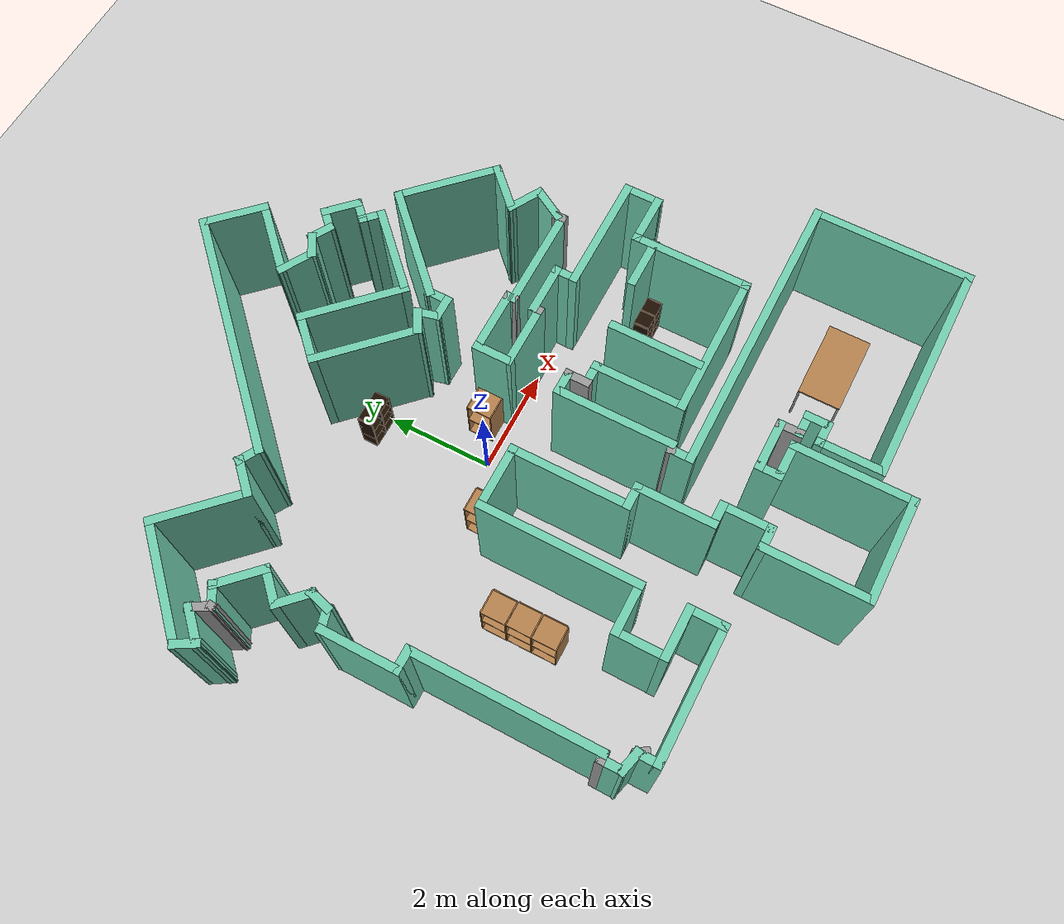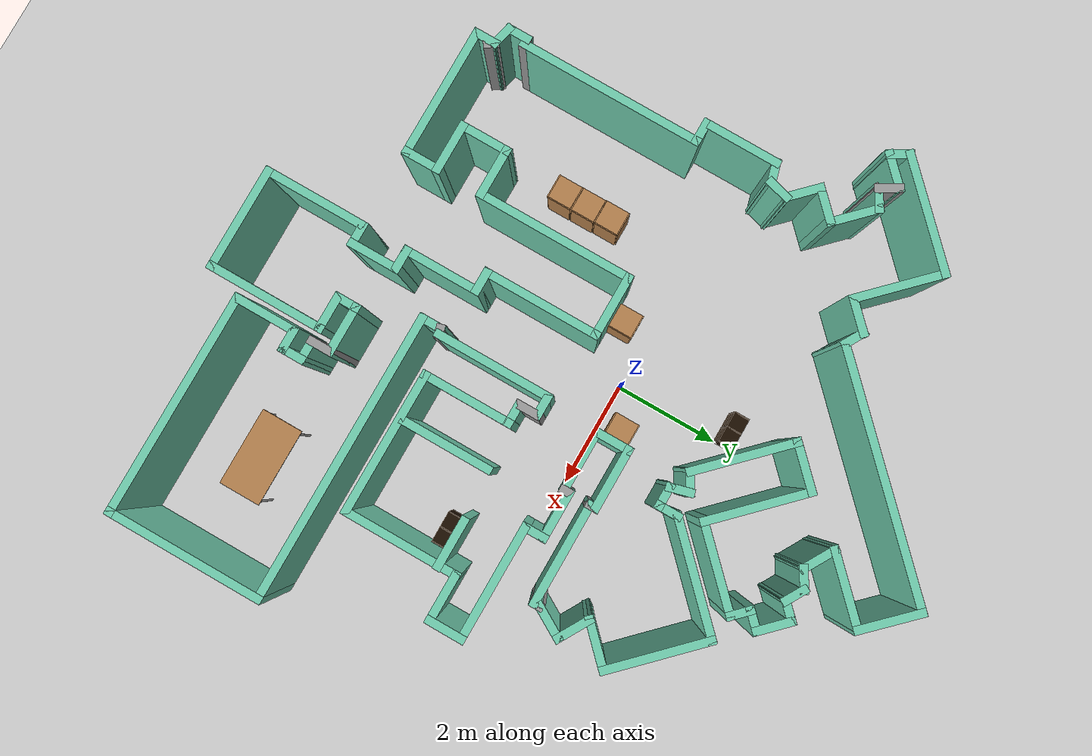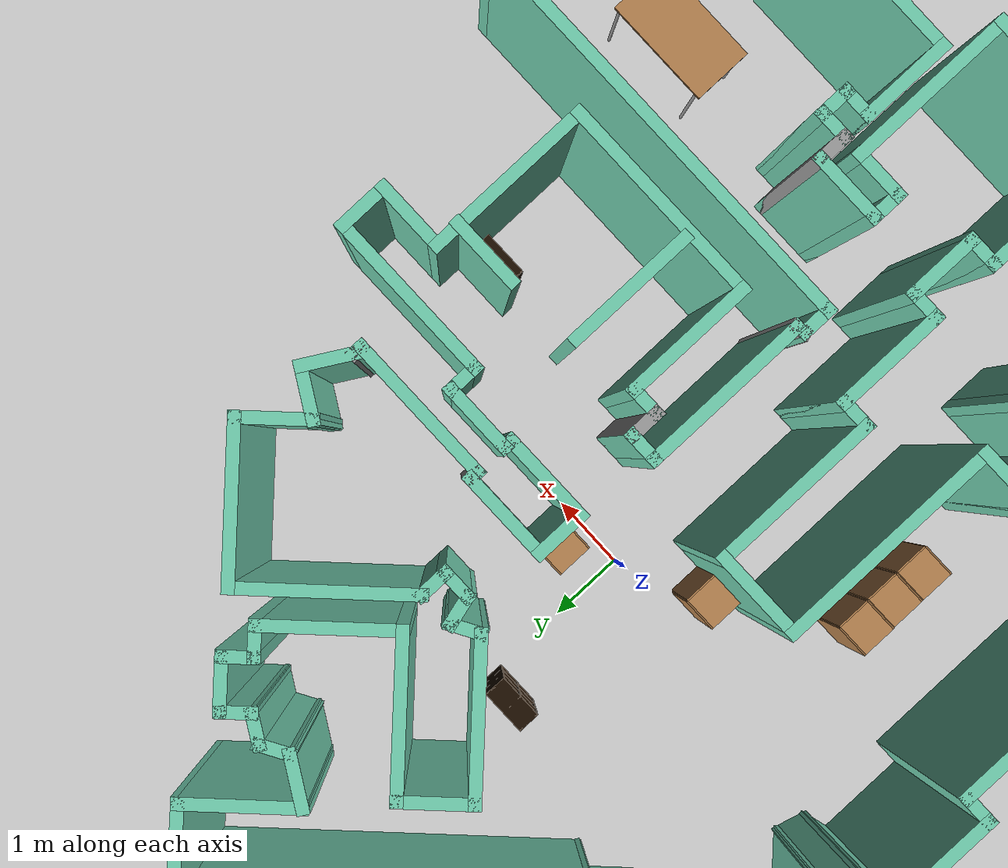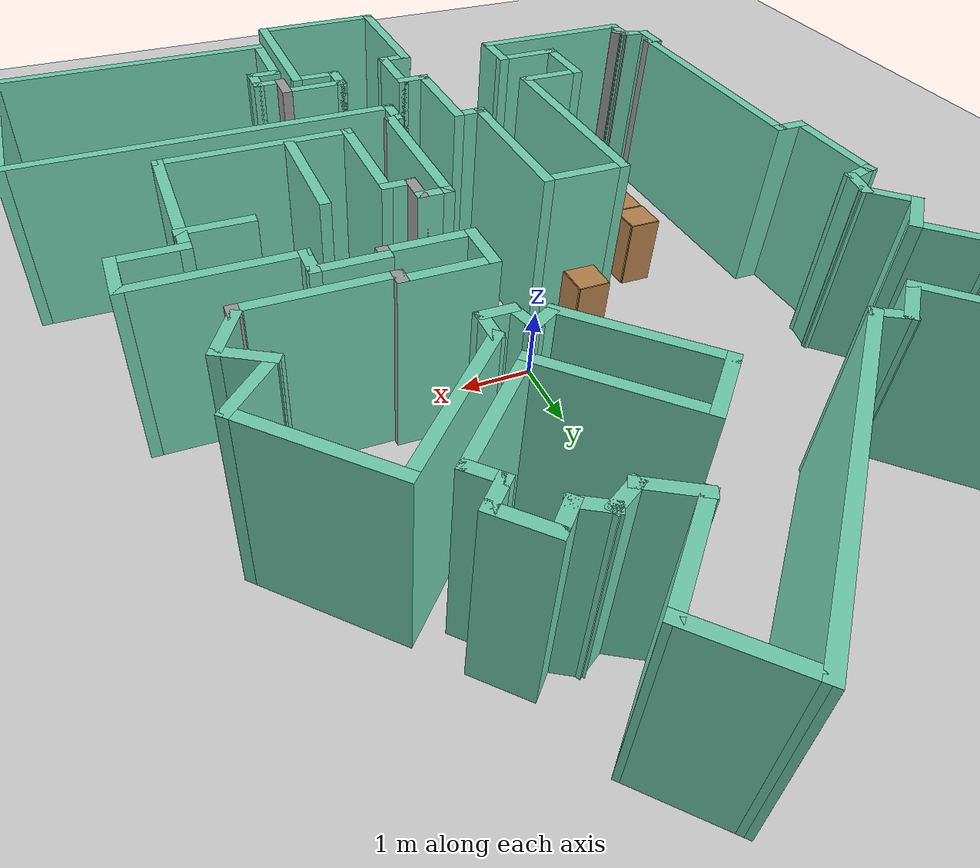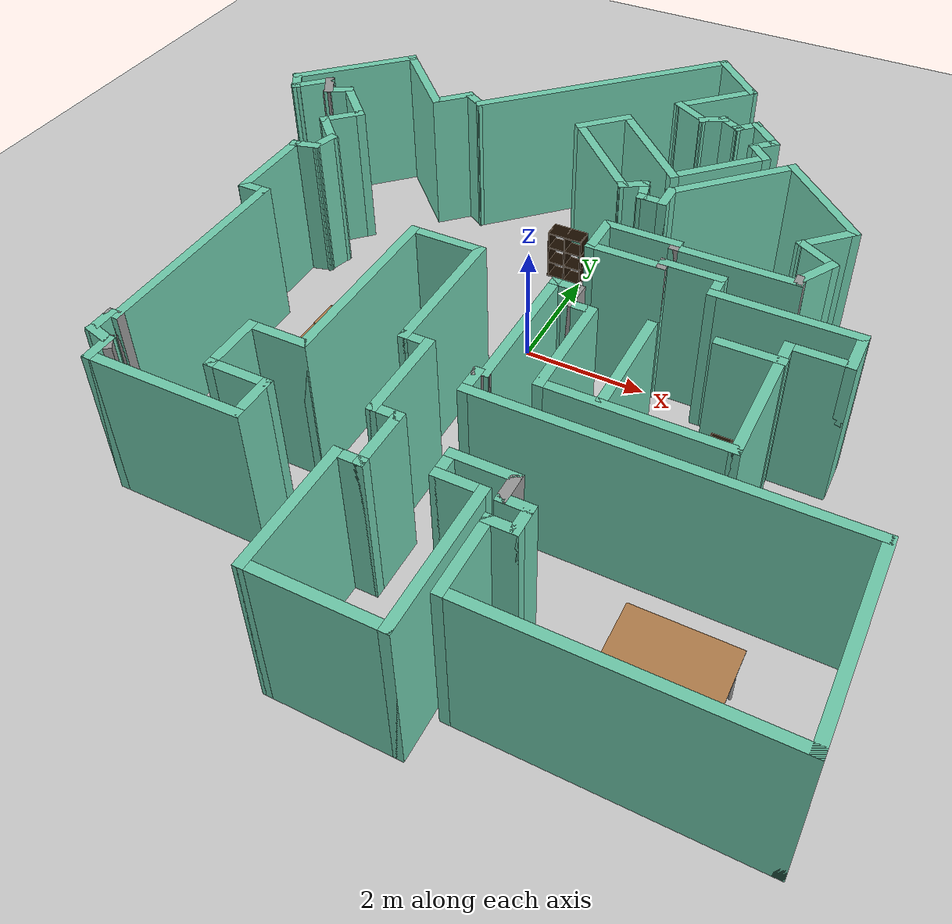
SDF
<sdf version="1.6">
 <world name="default">
  <light name="sun" type="directional">
   <pose>0 0 10 0 -0 0</pose>
   <diffuse>0.8 0.8 0.8 1</diffuse>
   <specular>0.2 0.2 0.2 1</specular>
   <attenuation>
    <range>1000</range>
    <constant>0.9</constant>
    <linear>0.01</linear>
    <quadratic>0.001</quadratic>
   </attenuation>
   <direction>-0.5 0.1 -0.9</direction>
  </light>
  <model name="ground_plane">
   <static>1</static>
   <link name="link">
    <collision name="collision">
     <geometry><plane><normal>0 0 1</normal><size>100 100</size></plane></geometry>
     <surface><friction><ode><mu>100</mu><mu2>50</mu2></ode></friction></surface>
    </collision>
    <visual name="visual">
     <cast_shadows>0</cast_shadows>
     <geometry><plane><normal>0 0 1</normal><size>100 100</size></plane></geometry>
     <material>
      <script><uri>file://media/materials/scripts/gazebo.material</uri><name>Gazebo/Grey</name></script>
     </material>
    </visual>
   </link>
  </model>
  <gravity>0 0 -9.8</gravity>
  <magnetic_field>6e-06 2.3e-05 -4.2e-05</magnetic_field>
  <atmosphere type="adiabatic"/>
  <physics name="default_physics" default="0" type="ode">
   <max_step_size>0.001</max_step_size>
   <real_time_factor>1</real_time_factor>
   <real_time_update_rate>1000</real_time_update_rate>
  </physics>
  <scene><ambient>0.4 0.4 0.4 1</ambient><background>0.7 0.7 0.7 1</background><shadows>1</shadows></scene>
  <spherical_coordinates>
   <surface_model>EARTH_WGS84</surface_model>
   <latitude_deg>0</latitude_deg>
   <longitude_deg>0</longitude_deg>
   <elevation>0</elevation>
   <heading_deg>0</heading_deg>
  </spherical_coordinates>
  <model name="map_11">
   <pose>0.213911 -0.396014 0 0 -0 0</pose>
   <link name="Wall_0">
    <collision name="Wall_0_Collision">
     <geometry><box><size>4.75 0.15 2.5</size></box></geometry>
     <pose>0 0 1.25 0 -0 0</pose>
    </collision>
    <visual name="Wall_0_Visual">
     <pose>0 0 1.25 0 -0 0</pose>
     <geometry><box><size>4.75 0.15 2.5</size></box></geometry>
     <material>
      <script><uri>file://media/materials/scripts/gazebo.material</uri><name>Gazebo/Grey</name></script>
      <ambient>0.435294 0.796078 0.67451 1</ambient>
     </material>
     <meta><layer>0</layer></meta>
    </visual>
    <pose>-0.933367 4.89876 0 0 -0 -2.35619</pose>
   </link>
   <link name="Wall_1">
    <collision name="Wall_1_Collision">
     <geometry><box><size>0.5 0.15 2.5</size></box></geometry>
     <pose>0 0 1.25 0 -0 0</pose>
    </collision>
    <visual name="Wall_1_Visual">
     <pose>0 0 1.25 0 -0 0</pose>
     <geometry><box><size>0.5 0.15 2.5</size></box></geometry>
     <material>
      <script><uri>file://media/materials/scripts/gazebo.material</uri><name>Gazebo/Grey</name></script>
      <ambient>0.435294 0.796078 0.67451 1</ambient>
     </material>
     <meta><layer>0</layer></meta>
    </visual>
    <pose>-2.71127 3.35991 0 0 -0 2.61799</pose>
   </link>
   <link name="Wall_10">
    <collision name="Wall_10_Collision">
     <geometry><box><size>1 0.15 2.5</size></box></geometry>
     <pose>0 0 1.25 0 -0 0</pose>
    </collision>
    <visual name="Wall_10_Visual">
     <pose>0 0 1.25 0 -0 0</pose>
     <geometry><box><size>1 0.15 2.5</size></box></geometry>
     <material>
      <script><uri>file://media/materials/scripts/gazebo.material</uri><name>Gazebo/Grey</name></script>
      <ambient>0.435294 0.796078 0.67451 1</ambient>
     </material>
     <meta><layer>0</layer></meta>
    </visual>
    <pose>-4.52549 2.36212 0 0 -0 -0.785398</pose>
   </link>
   <link name="Wall_100">
    <collision name="Wall_100_Collision">
     <geometry><box><size>1.25445 0.15 2.5</size></box></geometry>
     <pose>0 0 1.25 0 -0 0</pose>
    </collision>
    <visual name="Wall_100_Visual">
     <pose>0 0 1.25 0 -0 0</pose>
     <geometry><box><size>1.25445 0.15 2.5</size></box></geometry>
     <material>
      <script><uri>file://media/materials/scripts/gazebo.material</uri><name>Gazebo/Grey</name></script>
      <ambient>0.435294 0.796078 0.67451 1</ambient>
     </material>
     <meta><layer>0</layer></meta>
    </visual>
    <pose>1.07905 6.13026 0 0 -0 2.34496</pose>
   </link>
   <link name="Wall_102">
    <collision name="Wall_102_Collision">
     <geometry><box><size>1.75 0.15 2.5</size></box></geometry>
     <pose>0 0 1.25 0 -0 0</pose>
    </collision>
    <visual name="Wall_102_Visual">
     <pose>0 0 1.25 0 -0 0</pose>
     <geometry><box><size>1.75 0.15 2.5</size></box></geometry>
     <material>
      <script><uri>file://media/materials/scripts/gazebo.material</uri><name>Gazebo/Grey</name></script>
      <ambient>0.435294 0.796078 0.67451 1</ambient>
     </material>
     <meta><layer>0</layer></meta>
    </visual>
    <pose>2.21384 -1.64657 0 0 -0 1.5708</pose>
   </link>
   <link name="Wall_104">
    <collision name="Wall_104_Collision">
     <geometry><box><size>1 0.15 2.5</size></box></geometry>
     <pose>0 0 1.25 0 -0 0</pose>
    </collision>
    <visual name="Wall_104_Visual">
     <pose>0 0 1.25 0 -0 0</pose>
     <geometry><box><size>1 0.15 2.5</size></box></geometry>
     <material>
      <script><uri>file://media/materials/scripts/gazebo.material</uri><name>Gazebo/Grey</name></script>
      <ambient>0.435294 0.796078 0.67451 1</ambient>
     </material>
     <meta><layer>0</layer></meta>
    </visual>
    <pose>3.5727 -0.757031 0 0 -0 0</pose>
   </link>
   <link name="Wall_11">
    <collision name="Wall_11_Collision">
     <geometry><box><size>0.75 0.15 2.5</size></box></geometry>
     <pose>0 0 1.25 0 -0 0</pose>
    </collision>
    <visual name="Wall_11_Visual">
     <pose>0 0 1.25 0 -0 0</pose>
     <geometry><box><size>0.75 0.15 2.5</size></box></geometry>
     <material>
      <script><uri>file://media/materials/scripts/gazebo.material</uri><name>Gazebo/Grey</name></script>
      <ambient>0.435294 0.796078 0.67451 1</ambient>
     </material>
     <meta><layer>0</layer></meta>
    </visual>
    <pose>-4.4371 1.84947 0 0 -0 -2.35619</pose>
   </link>
   <link name="Wall_12">
    <collision name="Wall_12_Collision">
     <geometry><box><size>0.75 0.15 2.5</size></box></geometry>
     <pose>0 0 1.25 0 -0 0</pose>
    </collision>
    <visual name="Wall_12_Visual">
     <pose>0 0 1.25 0 -0 0</pose>
     <geometry><box><size>0.75 0.15 2.5</size></box></geometry>
     <material>
      <script><uri>file://media/materials/scripts/gazebo.material</uri><name>Gazebo/Grey</name></script>
      <ambient>0.435294 0.796078 0.67451 1</ambient>
     </material>
     <meta><layer>0</layer></meta>
    </visual>
    <pose>-4.4371 1.42521 0 0 -0 -0.785398</pose>
   </link>
   <link name="Wall_13">
    <collision name="Wall_13_Collision">
     <geometry><box><size>0.5 0.15 2.5</size></box></geometry>
     <pose>0 0 1.25 0 -0 0</pose>
    </collision>
    <visual name="Wall_13_Visual">
     <pose>0 0 1.25 0 -0 0</pose>
     <geometry><box><size>0.5 0.15 2.5</size></box></geometry>
     <material>
      <script><uri>file://media/materials/scripts/gazebo.material</uri><name>Gazebo/Grey</name></script>
      <ambient>0.435294 0.796078 0.67451 1</ambient>
     </material>
     <meta><layer>0</layer></meta>
    </visual>
    <pose>-4.27026 1.04404 0 0 -0 -1.8326</pose>
   </link>
   <link name="Wall_14">
    <collision name="Wall_14_Collision">
     <geometry><box><size>0.5 0.15 2.5</size></box></geometry>
     <pose>0 0 1.25 0 -0 0</pose>
    </collision>
    <visual name="Wall_14_Visual">
     <pose>0 0 1.25 0 -0 0</pose>
     <geometry><box><size>0.5 0.15 2.5</size></box></geometry>
     <material>
      <script><uri>file://media/materials/scripts/gazebo.material</uri><name>Gazebo/Grey</name></script>
      <ambient>0.435294 0.796078 0.67451 1</ambient>
     </material>
     <meta><layer>0</layer></meta>
    </visual>
    <pose>-4.48459 0.829708 0 0 -0 -2.87979</pose>
   </link>
   <link name="Wall_15">
    <collision name="Wall_15_Collision">
     <geometry><box><size>1.5 0.15 2.5</size></box></geometry>
     <pose>0 0 1.25 0 -0 0</pose>
    </collision>
    <visual name="Wall_15_Visual">
     <pose>0 0 1.25 0 -0 0</pose>
     <geometry><box><size>1.5 0.15 2.5</size></box></geometry>
     <material>
      <script><uri>file://media/materials/scripts/gazebo.material</uri><name>Gazebo/Grey</name></script>
      <ambient>0.435294 0.796078 0.67451 1</ambient>
     </material>
     <meta><layer>0</layer></meta>
    </visual>
    <pose>-4.65363 0.109414 0 0 -0 -1.5708</pose>
   </link>
   <link name="Wall_16">
    <collision name="Wall_16_Collision">
     <geometry><box><size>0.5 0.15 2.5</size></box></geometry>
     <pose>0 0 1.25 0 -0 0</pose>
    </collision>
    <visual name="Wall_16_Visual">
     <pose>0 0 1.25 0 -0 0</pose>
     <geometry><box><size>0.5 0.15 2.5</size></box></geometry>
     <material>
      <script><uri>file://media/materials/scripts/gazebo.material</uri><name>Gazebo/Grey</name></script>
      <ambient>0.435294 0.796078 0.67451 1</ambient>
     </material>
     <meta><layer>0</layer></meta>
    </visual>
    <pose>-4.47863 -0.565586 0 0 -0 0</pose>
   </link>
   <link name="Wall_17">
    <collision name="Wall_17_Collision">
     <geometry><box><size>3.5 0.15 2.5</size></box></geometry>
     <pose>0 0 1.25 0 -0 0</pose>
    </collision>
    <visual name="Wall_17_Visual">
     <pose>0 0 1.25 0 -0 0</pose>
     <geometry><box><size>3.5 0.15 2.5</size></box></geometry>
     <material>
      <script><uri>file://media/materials/scripts/gazebo.material</uri><name>Gazebo/Grey</name></script>
      <ambient>0.435294 0.796078 0.67451 1</ambient>
     </material>
     <meta><layer>0</layer></meta>
    </visual>
    <pose>-4.30363 -2.24059 0 0 -0 -1.5708</pose>
   </link>
   <link name="Wall_18">
    <collision name="Wall_18_Collision">
     <geometry><box><size>0.25 0.15 2.5</size></box></geometry>
     <pose>0 0 1.25 0 -0 0</pose>
    </collision>
    <visual name="Wall_18_Visual">
     <pose>0 0 1.25 0 -0 0</pose>
     <geometry><box><size>0.25 0.15 2.5</size></box></geometry>
     <material>
      <script><uri>file://media/materials/scripts/gazebo.material</uri><name>Gazebo/Grey</name></script>
      <ambient>1 1 1 1</ambient>
     </material>
     <meta><layer>0</layer></meta>
    </visual>
    <pose>-4.35363 -3.91559 0 0 -0 3.14159</pose>
   </link>
   <link name="Wall_19">
    <collision name="Wall_19_Collision">
     <geometry><box><size>0.5 0.15 2.5</size></box></geometry>
     <pose>0 0 1.25 0 -0 0</pose>
    </collision>
    <visual name="Wall_19_Visual">
     <pose>0 0 1.25 0 -0 0</pose>
     <geometry><box><size>0.5 0.15 2.5</size></box></geometry>
     <material>
      <script><uri>file://media/materials/scripts/gazebo.material</uri><name>Gazebo/Grey</name></script>
      <ambient>0.435294 0.796078 0.67451 1</ambient>
     </material>
     <meta><layer>0</layer></meta>
    </visual>
    <pose>-4.40363 -4.09059 0 0 -0 -1.5708</pose>
   </link>
   <link name="Wall_2">
    <collision name="Wall_2_Collision">
     <geometry><box><size>0.75 0.15 2.5</size></box></geometry>
     <pose>0 0 1.25 0 -0 0</pose>
    </collision>
    <visual name="Wall_2_Visual">
     <pose>0 0 1.25 0 -0 0</pose>
     <geometry><box><size>0.75 0.15 2.5</size></box></geometry>
     <material>
      <script><uri>file://media/materials/scripts/gazebo.material</uri><name>Gazebo/Grey</name></script>
      <ambient>0.435294 0.796078 0.67451 1</ambient>
     </material>
     <meta><layer>0</layer></meta>
    </visual>
    <pose>-3.07495 3.23528 0 0 -0 -2.35619</pose>
   </link>
   <link name="Wall_20">
    <collision name="Wall_20_Collision">
     <geometry><box><size>0.5 0.15 2.5</size></box></geometry>
     <pose>0 0 1.25 0 -0 0</pose>
    </collision>
    <visual name="Wall_20_Visual">
     <pose>0 0 1.25 0 -0 0</pose>
     <geometry><box><size>0.5 0.15 2.5</size></box></geometry>
     <material>
      <script><uri>file://media/materials/scripts/gazebo.material</uri><name>Gazebo/Grey</name></script>
      <ambient>0.435294 0.796078 0.67451 1</ambient>
     </material>
     <meta><layer>0</layer></meta>
    </visual>
    <pose>-4.23459 -4.31088 0 0 -0 -0.261799</pose>
   </link>
   <link name="Wall_21">
    <collision name="Wall_21_Collision">
     <geometry><box><size>0.271718 0.15 2.5</size></box></geometry>
     <pose>0 0 1.25 0 -0 0</pose>
    </collision>
    <visual name="Wall_21_Visual">
     <pose>0 0 1.25 0 -0 0</pose>
     <geometry><box><size>0.271718 0.15 2.5</size></box></geometry>
     <material>
      <script><uri>file://media/materials/scripts/gazebo.material</uri><name>Gazebo/Grey</name></script>
      <ambient>1 1 1 1</ambient>
     </material>
     <meta><layer>0</layer></meta>
    </visual>
    <pose>-4.03086 -4.40617 0 0 -0 -0.964164</pose>
   </link>
   <link name="Wall_27">
    <collision name="Wall_27_Collision">
     <geometry><box><size>0.5 0.15 2.5</size></box></geometry>
     <pose>0 0 1.25 0 -0 0</pose>
    </collision>
    <visual name="Wall_27_Visual">
     <pose>0 0 1.25 0 -0 0</pose>
     <geometry><box><size>0.5 0.15 2.5</size></box></geometry>
     <material>
      <script><uri>file://media/materials/scripts/gazebo.material</uri><name>Gazebo/Grey</name></script>
      <ambient>0.435294 0.796078 0.67451 1</ambient>
     </material>
     <meta><layer>0</layer></meta>
    </visual>
    <pose>-4.06555 -4.53117 0 0 -0 -1.5708</pose>
   </link>
   <link name="Wall_28">
    <collision name="Wall_28_Collision">
     <geometry><box><size>2.5 0.15 2.5</size></box></geometry>
     <pose>0 0 1.25 0 -0 0</pose>
    </collision>
    <visual name="Wall_28_Visual">
     <pose>0 0 1.25 0 -0 0</pose>
     <geometry><box><size>2.5 0.15 2.5</size></box></geometry>
     <material>
      <script><uri>file://media/materials/scripts/gazebo.material</uri><name>Gazebo/Grey</name></script>
      <ambient>0.435294 0.796078 0.67451 1</ambient>
     </material>
     <meta><layer>0</layer></meta>
    </visual>
    <pose>-2.89055 -4.70617 0 0 -0 0</pose>
   </link>
   <link name="Wall_29">
    <collision name="Wall_29_Collision">
     <geometry><box><size>0.75 0.15 2.5</size></box></geometry>
     <pose>0 0 1.25 0 -0 0</pose>
    </collision>
    <visual name="Wall_29_Visual">
     <pose>0 0 1.25 0 -0 0</pose>
     <geometry><box><size>0.75 0.15 2.5</size></box></geometry>
     <material>
      <script><uri>file://media/materials/scripts/gazebo.material</uri><name>Gazebo/Grey</name></script>
      <ambient>0.435294 0.796078 0.67451 1</ambient>
     </material>
     <meta><layer>0</layer></meta>
    </visual>
    <pose>-1.71555 -4.40617 0 0 -0 1.5708</pose>
   </link>
   <link name="Wall_3">
    <collision name="Wall_3_Collision">
     <geometry><box><size>1.75 0.15 2.5</size></box></geometry>
     <pose>0 0 1.25 0 -0 0</pose>
    </collision>
    <visual name="Wall_3_Visual">
     <pose>0 0 1.25 0 -0 0</pose>
     <geometry><box><size>1.75 0.15 2.5</size></box></geometry>
     <material>
      <script><uri>file://media/materials/scripts/gazebo.material</uri><name>Gazebo/Grey</name></script>
      <ambient>0.435294 0.796078 0.67451 1</ambient>
     </material>
     <meta><layer>0</layer></meta>
    </visual>
    <pose>-3.85277 3.58884 0 0 -0 2.35619</pose>
   </link>
   <link name="Wall_30">
    <collision name="Wall_30_Collision">
     <geometry><box><size>1 0.15 2.5</size></box></geometry>
     <pose>0 0 1.25 0 -0 0</pose>
    </collision>
    <visual name="Wall_30_Visual">
     <pose>0 0 1.25 0 -0 0</pose>
     <geometry><box><size>1 0.15 2.5</size></box></geometry>
     <material>
      <script><uri>file://media/materials/scripts/gazebo.material</uri><name>Gazebo/Grey</name></script>
      <ambient>0.435294 0.796078 0.67451 1</ambient>
     </material>
     <meta><layer>0</layer></meta>
    </visual>
    <pose>-2.14055 -4.10617 0 0 -0 3.14159</pose>
   </link>
   <link name="Wall_31">
    <collision name="Wall_31_Collision">
     <geometry><box><size>1 0.15 2.5</size></box></geometry>
     <pose>0 0 1.25 0 -0 0</pose>
    </collision>
    <visual name="Wall_31_Visual">
     <pose>0 0 1.25 0 -0 0</pose>
     <geometry><box><size>1 0.15 2.5</size></box></geometry>
     <material>
      <script><uri>file://media/materials/scripts/gazebo.material</uri><name>Gazebo/Grey</name></script>
      <ambient>0.435294 0.796078 0.67451 1</ambient>
     </material>
     <meta><layer>0</layer></meta>
    </visual>
    <pose>-2.56555 -3.68117 0 0 -0 1.5708</pose>
   </link>
   <link name="Wall_32">
    <collision name="Wall_32_Collision">
     <geometry><box><size>1 0.15 2.5</size></box></geometry>
     <pose>0 0 1.25 0 -0 0</pose>
    </collision>
    <visual name="Wall_32_Visual">
     <pose>0 0 1.25 0 -0 0</pose>
     <geometry><box><size>1 0.15 2.5</size></box></geometry>
     <material>
      <script><uri>file://media/materials/scripts/gazebo.material</uri><name>Gazebo/Grey</name></script>
      <ambient>0.435294 0.796078 0.67451 1</ambient>
     </material>
     <meta><layer>0</layer></meta>
    </visual>
    <pose>-2.14055 -3.25617 0 0 -0 0</pose>
   </link>
   <link name="Wall_33">
    <collision name="Wall_33_Collision">
     <geometry><box><size>3 0.15 2.5</size></box></geometry>
     <pose>0 0 1.25 0 -0 0</pose>
    </collision>
    <visual name="Wall_33_Visual">
     <pose>0 0 1.25 0 -0 0</pose>
     <geometry><box><size>3 0.15 2.5</size></box></geometry>
     <material>
      <script><uri>file://media/materials/scripts/gazebo.material</uri><name>Gazebo/Grey</name></script>
      <ambient>0.435294 0.796078 0.67451 1</ambient>
     </material>
     <meta><layer>0</layer></meta>
    </visual>
    <pose>-1.71555 -1.83117 0 0 -0 1.5708</pose>
   </link>
   <link name="Wall_34">
    <collision name="Wall_34_Collision">
     <geometry><box><size>1.25 0.15 2.5</size></box></geometry>
     <pose>0 0 1.25 0 -0 0</pose>
    </collision>
    <visual name="Wall_34_Visual">
     <pose>0 0 1.25 0 -0 0</pose>
     <geometry><box><size>1.25 0.15 2.5</size></box></geometry>
     <material>
      <script><uri>file://media/materials/scripts/gazebo.material</uri><name>Gazebo/Grey</name></script>
      <ambient>0.435294 0.796078 0.67451 1</ambient>
     </material>
     <meta><layer>0</layer></meta>
    </visual>
    <pose>-1.16555 -0.406172 0 0 -0 0</pose>
   </link>
   <link name="Wall_35">
    <collision name="Wall_35_Collision">
     <geometry><box><size>2.25 0.15 2.5</size></box></geometry>
     <pose>0 0 1.25 0 -0 0</pose>
    </collision>
    <visual name="Wall_35_Visual">
     <pose>0 0 1.25 0 -0 0</pose>
     <geometry><box><size>2.25 0.15 2.5</size></box></geometry>
     <material>
      <script><uri>file://media/materials/scripts/gazebo.material</uri><name>Gazebo/Grey</name></script>
      <ambient>0.435294 0.796078 0.67451 1</ambient>
     </material>
     <meta><layer>0</layer></meta>
    </visual>
    <pose>-0.615553 -1.45617 0 0 -0 -1.5708</pose>
   </link>
   <link name="Wall_36">
    <collision name="Wall_36_Collision">
     <geometry><box><size>0.5 0.15 2.5</size></box></geometry>
     <pose>0 0 1.25 0 -0 0</pose>
    </collision>
    <visual name="Wall_36_Visual">
     <pose>0 0 1.25 0 -0 0</pose>
     <geometry><box><size>0.5 0.15 2.5</size></box></geometry>
     <material>
      <script><uri>file://media/materials/scripts/gazebo.material</uri><name>Gazebo/Grey</name></script>
      <ambient>0.435294 0.796078 0.67451 1</ambient>
     </material>
     <meta><layer>0</layer></meta>
    </visual>
    <pose>-0.440553 -2.50617 0 0 -0 0</pose>
   </link>
   <link name="Wall_37">
    <collision name="Wall_37_Collision">
     <geometry><box><size>1.5 0.15 2.5</size></box></geometry>
     <pose>0 0 1.25 0 -0 0</pose>
    </collision>
    <visual name="Wall_37_Visual">
     <pose>0 0 1.25 0 -0 0</pose>
     <geometry><box><size>1.5 0.15 2.5</size></box></geometry>
     <material>
      <script><uri>file://media/materials/scripts/gazebo.material</uri><name>Gazebo/Grey</name></script>
      <ambient>0.435294 0.796078 0.67451 1</ambient>
     </material>
     <meta><layer>0</layer></meta>
    </visual>
    <pose>-0.265553 -3.18117 0 0 -0 -1.5708</pose>
   </link>
   <link name="Wall_38">
    <collision name="Wall_38_Collision">
     <geometry><box><size>0.5 0.15 2.5</size></box></geometry>
     <pose>0 0 1.25 0 -0 0</pose>
    </collision>
    <visual name="Wall_38_Visual">
     <pose>0 0 1.25 0 -0 0</pose>
     <geometry><box><size>0.5 0.15 2.5</size></box></geometry>
     <material>
      <script><uri>file://media/materials/scripts/gazebo.material</uri><name>Gazebo/Grey</name></script>
      <ambient>0.435294 0.796078 0.67451 1</ambient>
     </material>
     <meta><layer>0</layer></meta>
    </visual>
    <pose>-0.090554 -3.85617 0 0 -0 0</pose>
   </link>
   <link name="Wall_39">
    <collision name="Wall_39_Collision">
     <geometry><box><size>1 0.15 2.5</size></box></geometry>
     <pose>0 0 1.25 0 -0 0</pose>
    </collision>
    <visual name="Wall_39_Visual">
     <pose>0 0 1.25 0 -0 0</pose>
     <geometry><box><size>1 0.15 2.5</size></box></geometry>
     <material>
      <script><uri>file://media/materials/scripts/gazebo.material</uri><name>Gazebo/Grey</name></script>
      <ambient>0.435294 0.796078 0.67451 1</ambient>
     </material>
     <meta><layer>0</layer></meta>
    </visual>
    <pose>0.084447 -4.28117 0 0 -0 -1.5708</pose>
   </link>
   <link name="Wall_4">
    <collision name="Wall_4_Collision">
     <geometry><box><size>2.25 0.15 2.5</size></box></geometry>
     <pose>0 0 1.25 0 -0 0</pose>
    </collision>
    <visual name="Wall_4_Visual">
     <pose>0 0 1.25 0 -0 0</pose>
     <geometry><box><size>2.25 0.15 2.5</size></box></geometry>
     <material>
      <script><uri>file://media/materials/scripts/gazebo.material</uri><name>Gazebo/Grey</name></script>
      <ambient>0.435294 0.796078 0.67451 1</ambient>
     </material>
     <meta><layer>0</layer></meta>
    </visual>
    <pose>-5.16092 3.41206 0 0 -0 -2.35619</pose>
   </link>
   <link name="Wall_40">
    <collision name="Wall_40_Collision">
     <geometry><box><size>0.5 0.15 2.5</size></box></geometry>
     <pose>0 0 1.25 0 -0 0</pose>
    </collision>
    <visual name="Wall_40_Visual">
     <pose>0 0 1.25 0 -0 0</pose>
     <geometry><box><size>0.5 0.15 2.5</size></box></geometry>
     <material>
      <script><uri>file://media/materials/scripts/gazebo.material</uri><name>Gazebo/Grey</name></script>
      <ambient>0.435294 0.796078 0.67451 1</ambient>
     </material>
     <meta><layer>0</layer></meta>
    </visual>
    <pose>-0.090554 -4.70617 0 0 -0 3.14159</pose>
   </link>
   <link name="Wall_41">
    <collision name="Wall_41_Collision">
     <geometry><box><size>2 0.15 2.5</size></box></geometry>
     <pose>0 0 1.25 0 -0 0</pose>
    </collision>
    <visual name="Wall_41_Visual">
     <pose>0 0 1.25 0 -0 0</pose>
     <geometry><box><size>2 0.15 2.5</size></box></geometry>
     <material>
      <script><uri>file://media/materials/scripts/gazebo.material</uri><name>Gazebo/Grey</name></script>
      <ambient>0.435294 0.796078 0.67451 1</ambient>
     </material>
     <meta><layer>0</layer></meta>
    </visual>
    <pose>-0.265553 -5.63117 0 0 -0 -1.5708</pose>
   </link>
   <link name="Wall_42">
    <collision name="Wall_42_Collision">
     <geometry><box><size>2 0.15 2.5</size></box></geometry>
     <pose>0 0 1.25 0 -0 0</pose>
    </collision>
    <visual name="Wall_42_Visual">
     <pose>0 0 1.25 0 -0 0</pose>
     <geometry><box><size>2 0.15 2.5</size></box></geometry>
     <material>
      <script><uri>file://media/materials/scripts/gazebo.material</uri><name>Gazebo/Grey</name></script>
      <ambient>0.435294 0.796078 0.67451 1</ambient>
     </material>
     <meta><layer>0</layer></meta>
    </visual>
    <pose>0.659447 -6.55617 0 0 -0 0</pose>
   </link>
   <link name="Wall_43">
    <collision name="Wall_43_Collision">
     <geometry><box><size>2.25 0.15 2.5</size></box></geometry>
     <pose>0 0 1.25 0 -0 0</pose>
    </collision>
    <visual name="Wall_43_Visual">
     <pose>0 0 1.25 0 -0 0</pose>
     <geometry><box><size>2.25 0.15 2.5</size></box></geometry>
     <material>
      <script><uri>file://media/materials/scripts/gazebo.material</uri><name>Gazebo/Grey</name></script>
      <ambient>0.435294 0.796078 0.67451 1</ambient>
     </material>
     <meta><layer>0</layer></meta>
    </visual>
    <pose>1.58445 -5.50617 0 0 -0 1.5708</pose>
   </link>
   <link name="Wall_44">
    <collision name="Wall_44_Collision">
     <geometry><box><size>0.75 0.15 2.5</size></box></geometry>
     <pose>0 0 1.25 0 -0 0</pose>
    </collision>
    <visual name="Wall_44_Visual">
     <pose>0 0 1.25 0 -0 0</pose>
     <geometry><box><size>0.75 0.15 2.5</size></box></geometry>
     <material>
      <script><uri>file://media/materials/scripts/gazebo.material</uri><name>Gazebo/Grey</name></script>
      <ambient>0.435294 0.796078 0.67451 1</ambient>
     </material>
     <meta><layer>0</layer></meta>
    </visual>
    <pose>1.28445 -4.45617 0 0 -0 3.14159</pose>
   </link>
   <link name="Wall_45">
    <collision name="Wall_45_Collision">
     <geometry><box><size>0.5 0.15 2.5</size></box></geometry>
     <pose>0 0 1.25 0 -0 0</pose>
    </collision>
    <visual name="Wall_45_Visual">
     <pose>0 0 1.25 0 -0 0</pose>
     <geometry><box><size>0.5 0.15 2.5</size></box></geometry>
     <material>
      <script><uri>file://media/materials/scripts/gazebo.material</uri><name>Gazebo/Grey</name></script>
      <ambient>0.435294 0.796078 0.67451 1</ambient>
     </material>
     <meta><layer>0</layer></meta>
    </visual>
    <pose>0.984447 -4.28117 0 0 -0 1.5708</pose>
   </link>
   <link name="Wall_46">
    <collision name="Wall_46_Collision">
     <geometry><box><size>1 0.15 2.5</size></box></geometry>
     <pose>0 0 1.25 0 -0 0</pose>
    </collision>
    <visual name="Wall_46_Visual">
     <pose>0 0 1.25 0 -0 0</pose>
     <geometry><box><size>1 0.15 2.5</size></box></geometry>
     <material>
      <script><uri>file://media/materials/scripts/gazebo.material</uri><name>Gazebo/Grey</name></script>
      <ambient>0.435294 0.796078 0.67451 1</ambient>
     </material>
     <meta><layer>0</layer></meta>
    </visual>
    <pose>1.40945 -4.10617 0 0 -0 0</pose>
   </link>
   <link name="Wall_47">
    <collision name="Wall_47_Collision">
     <geometry><box><size>0.5 0.15 2.5</size></box></geometry>
     <pose>0 0 1.25 0 -0 0</pose>
    </collision>
    <visual name="Wall_47_Visual">
     <pose>0 0 1.25 0 -0 0</pose>
     <geometry><box><size>0.5 0.15 2.5</size></box></geometry>
     <material>
      <script><uri>file://media/materials/scripts/gazebo.material</uri><name>Gazebo/Grey</name></script>
      <ambient>1 1 1 1</ambient>
     </material>
     <meta><layer>0</layer></meta>
    </visual>
    <pose>1.83445 -4.28117 0 0 -0 -1.5708</pose>
   </link>
   <link name="Wall_48">
    <collision name="Wall_48_Collision">
     <geometry><box><size>0.5 0.15 2.5</size></box></geometry>
     <pose>0 0 1.25 0 -0 0</pose>
    </collision>
    <visual name="Wall_48_Visual">
     <pose>0 0 1.25 0 -0 0</pose>
     <geometry><box><size>0.5 0.15 2.5</size></box></geometry>
     <material>
      <script><uri>file://media/materials/scripts/gazebo.material</uri><name>Gazebo/Grey</name></script>
      <ambient>0.435294 0.796078 0.67451 1</ambient>
     </material>
     <meta><layer>0</layer></meta>
    </visual>
    <pose>2.00945 -4.45617 0 0 -0 0</pose>
   </link>
   <link name="Wall_49">
    <collision name="Wall_49_Collision">
     <geometry><box><size>0.5 0.15 2.5</size></box></geometry>
     <pose>0 0 1.25 0 -0 0</pose>
    </collision>
    <visual name="Wall_49_Visual">
     <pose>0 0 1.25 0 -0 0</pose>
     <geometry><box><size>0.5 0.15 2.5</size></box></geometry>
     <material>
      <script><uri>file://media/materials/scripts/gazebo.material</uri><name>Gazebo/Grey</name></script>
      <ambient>0.435294 0.796078 0.67451 1</ambient>
     </material>
     <meta><layer>0</layer></meta>
    </visual>
    <pose>2.18445 -4.63117 0 0 -0 -1.5708</pose>
   </link>
   <link name="Wall_5">
    <collision name="Wall_5_Collision">
     <geometry><box><size>0.5 0.15 2.5</size></box></geometry>
     <pose>0 0 1.25 0 -0 0</pose>
    </collision>
    <visual name="Wall_5_Visual">
     <pose>0 0 1.25 0 -0 0</pose>
     <geometry><box><size>0.5 0.15 2.5</size></box></geometry>
     <material>
      <script><uri>file://media/materials/scripts/gazebo.material</uri><name>Gazebo/Grey</name></script>
      <ambient>0.435294 0.796078 0.67451 1</ambient>
     </material>
     <meta><layer>0</layer></meta>
    </visual>
    <pose>-5.81588 2.51804 0 0 -0 -1.0472</pose>
   </link>
   <link name="Wall_50">
    <collision name="Wall_50_Collision">
     <geometry><box><size>0.5 0.15 2.5</size></box></geometry>
     <pose>0 0 1.25 0 -0 0</pose>
    </collision>
    <visual name="Wall_50_Visual">
     <pose>0 0 1.25 0 -0 0</pose>
     <geometry><box><size>0.5 0.15 2.5</size></box></geometry>
     <material>
      <script><uri>file://media/materials/scripts/gazebo.material</uri><name>Gazebo/Grey</name></script>
      <ambient>0.435294 0.796078 0.67451 1</ambient>
     </material>
     <meta><layer>0</layer></meta>
    </visual>
    <pose>2.00945 -4.80617 0 0 -0 3.14159</pose>
   </link>
   <link name="Wall_51">
    <collision name="Wall_51_Collision">
     <geometry><box><size>1.25 0.15 2.5</size></box></geometry>
     <pose>0 0 1.25 0 -0 0</pose>
    </collision>
    <visual name="Wall_51_Visual">
     <pose>0 0 1.25 0 -0 0</pose>
     <geometry><box><size>1.25 0.15 2.5</size></box></geometry>
     <material>
      <script><uri>file://media/materials/scripts/gazebo.material</uri><name>Gazebo/Grey</name></script>
      <ambient>0.435294 0.796078 0.67451 1</ambient>
     </material>
     <meta><layer>0</layer></meta>
    </visual>
    <pose>1.83445 -5.35617 0 0 -0 -1.5708</pose>
   </link>
   <link name="Wall_52">
    <collision name="Wall_52_Collision">
     <geometry><box><size>4.25 0.15 2.5</size></box></geometry>
     <pose>0 0 1.25 0 -0 0</pose>
    </collision>
    <visual name="Wall_52_Visual">
     <pose>0 0 1.25 0 -0 0</pose>
     <geometry><box><size>4.25 0.15 2.5</size></box></geometry>
     <material>
      <script><uri>file://media/materials/scripts/gazebo.material</uri><name>Gazebo/Grey</name></script>
      <ambient>0.435294 0.796078 0.67451 1</ambient>
     </material>
     <meta><layer>0</layer></meta>
    </visual>
    <pose>3.88445 -5.90617 0 0 -0 0</pose>
   </link>
   <link name="Wall_53">
    <collision name="Wall_53_Collision">
     <geometry><box><size>3 0.15 2.5</size></box></geometry>
     <pose>0 0 1.25 0 -0 0</pose>
    </collision>
    <visual name="Wall_53_Visual">
     <pose>0 0 1.25 0 -0 0</pose>
     <geometry><box><size>3 0.15 2.5</size></box></geometry>
     <material>
      <script><uri>file://media/materials/scripts/gazebo.material</uri><name>Gazebo/Grey</name></script>
      <ambient>0.435294 0.796078 0.67451 1</ambient>
     </material>
     <meta><layer>0</layer></meta>
    </visual>
    <pose>5.93445 -4.48117 0 0 -0 1.5708</pose>
   </link>
   <link name="Wall_54">
    <collision name="Wall_54_Collision">
     <geometry><box><size>5.5 0.15 2.5</size></box></geometry>
     <pose>0 0 1.25 0 -0 0</pose>
    </collision>
    <visual name="Wall_54_Visual">
     <pose>0 0 1.25 0 -0 0</pose>
     <geometry><box><size>5.5 0.15 2.5</size></box></geometry>
     <material>
      <script><uri>file://media/materials/scripts/gazebo.material</uri><name>Gazebo/Grey</name></script>
      <ambient>0.435294 0.796078 0.67451 1</ambient>
     </material>
     <meta><layer>0</layer></meta>
    </visual>
    <pose>3.25945 -3.05617 0 0 -0 3.14159</pose>
   </link>
   <link name="Wall_55">
    <collision name="Wall_55_Collision">
     <geometry><box><size>0.5 0.15 2.5</size></box></geometry>
     <pose>0 0 1.25 0 -0 0</pose>
    </collision>
    <visual name="Wall_55_Visual">
     <pose>0 0 1.25 0 -0 0</pose>
     <geometry><box><size>0.5 0.15 2.5</size></box></geometry>
     <material>
      <script><uri>file://media/materials/scripts/gazebo.material</uri><name>Gazebo/Grey</name></script>
      <ambient>0.435294 0.796078 0.67451 1</ambient>
     </material>
     <meta><layer>0</layer></meta>
    </visual>
    <pose>0.584447 -2.88117 0 0 -0 1.5708</pose>
   </link>
   <link name="Wall_56">
    <collision name="Wall_56_Collision">
     <geometry><box><size>0.25 0.15 2.5</size></box></geometry>
     <pose>0 0 1.25 0 -0 0</pose>
    </collision>
    <visual name="Wall_56_Visual">
     <pose>0 0 1.25 0 -0 0</pose>
     <geometry><box><size>0.25 0.15 2.5</size></box></geometry>
     <material>
      <script><uri>file://media/materials/scripts/gazebo.material</uri><name>Gazebo/Grey</name></script>
      <ambient>1 1 1 1</ambient>
     </material>
     <meta><layer>0</layer></meta>
    </visual>
    <pose>0.632743 -2.69323 0 0 -0 0.261799</pose>
   </link>
   <link name="Wall_57">
    <collision name="Wall_57_Collision">
     <geometry><box><size>2.25 0.15 2.5</size></box></geometry>
     <pose>0 0 1.25 0 -0 0</pose>
    </collision>
    <visual name="Wall_57_Visual">
     <pose>0 0 1.25 0 -0 0</pose>
     <geometry><box><size>2.25 0.15 2.5</size></box></geometry>
     <material>
      <script><uri>file://media/materials/scripts/gazebo.material</uri><name>Gazebo/Grey</name></script>
      <ambient>0.435294 0.796078 0.67451 1</ambient>
     </material>
     <meta><layer>0</layer></meta>
    </visual>
    <pose>0.681039 -1.63029 0 0 -0 1.5708</pose>
   </link>
   <link name="Wall_58">
    <collision name="Wall_58_Collision">
     <geometry><box><size>0.5 0.15 2.5</size></box></geometry>
     <pose>0 0 1.25 0 -0 0</pose>
    </collision>
    <visual name="Wall_58_Visual">
     <pose>0 0 1.25 0 -0 0</pose>
     <geometry><box><size>0.5 0.15 2.5</size></box></geometry>
     <material>
      <script><uri>file://media/materials/scripts/gazebo.material</uri><name>Gazebo/Grey</name></script>
      <ambient>0.435294 0.796078 0.67451 1</ambient>
     </material>
     <meta><layer>0</layer></meta>
    </visual>
    <pose>0.856039 -0.580291 0 0 -0 0</pose>
   </link>
   <link name="Wall_59">
    <collision name="Wall_59_Collision">
     <geometry><box><size>0.5 0.15 2.5</size></box></geometry>
     <pose>0 0 1.25 0 -0 0</pose>
    </collision>
    <visual name="Wall_59_Visual">
     <pose>0 0 1.25 0 -0 0</pose>
     <geometry><box><size>0.5 0.15 2.5</size></box></geometry>
     <material>
      <script><uri>file://media/materials/scripts/gazebo.material</uri><name>Gazebo/Grey</name></script>
      <ambient>1 1 1 1</ambient>
     </material>
     <meta><layer>0</layer></meta>
    </visual>
    <pose>1.03104 -0.755291 0 0 -0 -1.5708</pose>
   </link>
   <link name="Wall_6">
    <collision name="Wall_6_Collision">
     <geometry><box><size>0.75 0.15 2.5</size></box></geometry>
     <pose>0 0 1.25 0 -0 0</pose>
    </collision>
    <visual name="Wall_6_Visual">
     <pose>0 0 1.25 0 -0 0</pose>
     <geometry><box><size>0.75 0.15 2.5</size></box></geometry>
     <material>
      <script><uri>file://media/materials/scripts/gazebo.material</uri><name>Gazebo/Grey</name></script>
      <ambient>0.435294 0.796078 0.67451 1</ambient>
     </material>
     <meta><layer>0</layer></meta>
    </visual>
    <pose>-5.51625 2.57862 0 0 -0 0.785398</pose>
   </link>
   <link name="Wall_60">
    <collision name="Wall_60_Collision">
     <geometry><box><size>0.5 0.15 2.5</size></box></geometry>
     <pose>0 0 1.25 0 -0 0</pose>
    </collision>
    <visual name="Wall_60_Visual">
     <pose>0 0 1.25 0 -0 0</pose>
     <geometry><box><size>0.5 0.15 2.5</size></box></geometry>
     <material>
      <script><uri>file://media/materials/scripts/gazebo.material</uri><name>Gazebo/Grey</name></script>
      <ambient>0.435294 0.796078 0.67451 1</ambient>
     </material>
     <meta><layer>0</layer></meta>
    </visual>
    <pose>1.20604 -0.930291 0 0 -0 0</pose>
   </link>
   <link name="Wall_61">
    <collision name="Wall_61_Collision">
     <geometry><box><size>1.75 0.15 2.5</size></box></geometry>
     <pose>0 0 1.25 0 -0 0</pose>
    </collision>
    <visual name="Wall_61_Visual">
     <pose>0 0 1.25 0 -0 0</pose>
     <geometry><box><size>1.75 0.15 2.5</size></box></geometry>
     <material>
      <script><uri>file://media/materials/scripts/gazebo.material</uri><name>Gazebo/Grey</name></script>
      <ambient>0.435294 0.796078 0.67451 1</ambient>
     </material>
     <meta><layer>0</layer></meta>
    </visual>
    <pose>1.38104 -1.73029 0 0 -0 -1.5708</pose>
   </link>
   <link name="Wall_62">
    <collision name="Wall_62_Collision">
     <geometry><box><size>2.75 0.15 2.5</size></box></geometry>
     <pose>0 0 1.25 0 -0 0</pose>
    </collision>
    <visual name="Wall_62_Visual">
     <pose>0 0 1.25 0 -0 0</pose>
     <geometry><box><size>2.75 0.15 2.5</size></box></geometry>
     <material>
      <script><uri>file://media/materials/scripts/gazebo.material</uri><name>Gazebo/Grey</name></script>
      <ambient>0.435294 0.796078 0.67451 1</ambient>
     </material>
     <meta><layer>0</layer></meta>
    </visual>
    <pose>2.68104 -2.53029 0 0 -0 0</pose>
   </link>
   <link name="Wall_63">
    <collision name="Wall_63_Collision">
     <geometry><box><size>2.25 0.15 2.5</size></box></geometry>
     <pose>0 0 1.25 0 -0 0</pose>
    </collision>
    <visual name="Wall_63_Visual">
     <pose>0 0 1.25 0 -0 0</pose>
     <geometry><box><size>2.25 0.15 2.5</size></box></geometry>
     <material>
      <script><uri>file://media/materials/scripts/gazebo.material</uri><name>Gazebo/Grey</name></script>
      <ambient>0.435294 0.796078 0.67451 1</ambient>
     </material>
     <meta><layer>0</layer></meta>
    </visual>
    <pose>3.98104 -1.48029 0 0 -0 1.5708</pose>
   </link>
   <link name="Wall_64">
    <collision name="Wall_64_Collision">
     <geometry><box><size>1 0.15 2.5</size></box></geometry>
     <pose>0 0 1.25 0 -0 0</pose>
    </collision>
    <visual name="Wall_64_Visual">
     <pose>0 0 1.25 0 -0 0</pose>
     <geometry><box><size>1 0.15 2.5</size></box></geometry>
     <material>
      <script><uri>file://media/materials/scripts/gazebo.material</uri><name>Gazebo/Grey</name></script>
      <ambient>0.435294 0.796078 0.67451 1</ambient>
     </material>
     <meta><layer>0</layer></meta>
    </visual>
    <pose>4.40604 -0.430291 0 0 -0 0</pose>
   </link>
   <link name="Wall_65">
    <collision name="Wall_65_Collision">
     <geometry><box><size>0.75 0.15 2.5</size></box></geometry>
     <pose>0 0 1.25 0 -0 0</pose>
    </collision>
    <visual name="Wall_65_Visual">
     <pose>0 0 1.25 0 -0 0</pose>
     <geometry><box><size>0.75 0.15 2.5</size></box></geometry>
     <material>
      <script><uri>file://media/materials/scripts/gazebo.material</uri><name>Gazebo/Grey</name></script>
      <ambient>0.435294 0.796078 0.67451 1</ambient>
     </material>
     <meta><layer>0</layer></meta>
    </visual>
    <pose>4.83104 -0.130291 0 0 -0 1.5708</pose>
   </link>
   <link name="Wall_66">
    <collision name="Wall_66_Collision">
     <geometry><box><size>2.25 0.15 2.5</size></box></geometry>
     <pose>0 0 1.25 0 -0 0</pose>
    </collision>
    <visual name="Wall_66_Visual">
     <pose>0 0 1.25 0 -0 0</pose>
     <geometry><box><size>2.25 0.15 2.5</size></box></geometry>
     <material>
      <script><uri>file://media/materials/scripts/gazebo.material</uri><name>Gazebo/Grey</name></script>
      <ambient>0.435294 0.796078 0.67451 1</ambient>
     </material>
     <meta><layer>0</layer></meta>
    </visual>
    <pose>3.78104 0.169709 0 0 -0 3.14159</pose>
   </link>
   <link name="Wall_67">
    <collision name="Wall_67_Collision">
     <geometry><box><size>0.5 0.15 2.5</size></box></geometry>
     <pose>0 0 1.25 0 -0 0</pose>
    </collision>
    <visual name="Wall_67_Visual">
     <pose>0 0 1.25 0 -0 0</pose>
     <geometry><box><size>0.5 0.15 2.5</size></box></geometry>
     <material>
      <script><uri>file://media/materials/scripts/gazebo.material</uri><name>Gazebo/Grey</name></script>
      <ambient>0.435294 0.796078 0.67451 1</ambient>
     </material>
     <meta><layer>0</layer></meta>
    </visual>
    <pose>2.73104 0.344709 0 0 -0 1.5708</pose>
   </link>
   <link name="Wall_68">
    <collision name="Wall_68_Collision">
     <geometry><box><size>1 0.15 2.5</size></box></geometry>
     <pose>0 0 1.25 0 -0 0</pose>
    </collision>
    <visual name="Wall_68_Visual">
     <pose>0 0 1.25 0 -0 0</pose>
     <geometry><box><size>1 0.15 2.5</size></box></geometry>
     <material>
      <script><uri>file://media/materials/scripts/gazebo.material</uri><name>Gazebo/Grey</name></script>
      <ambient>0.435294 0.796078 0.67451 1</ambient>
     </material>
     <meta><layer>0</layer></meta>
    </visual>
    <pose>2.30604 0.519709 0 0 -0 3.14159</pose>
   </link>
   <link name="Wall_69">
    <collision name="Wall_69_Collision">
     <geometry><box><size>0.25 0.15 2.5</size></box></geometry>
     <pose>0 0 1.25 0 -0 0</pose>
    </collision>
    <visual name="Wall_69_Visual">
     <pose>0 0 1.25 0 -0 0</pose>
     <geometry><box><size>0.25 0.15 2.5</size></box></geometry>
     <material>
      <script><uri>file://media/materials/scripts/gazebo.material</uri><name>Gazebo/Grey</name></script>
      <ambient>1 1 1 1</ambient>
     </material>
     <meta><layer>0</layer></meta>
    </visual>
    <pose>1.88104 0.469709 0 0 -0 -1.5708</pose>
   </link>
   <link name="Wall_7">
    <collision name="Wall_7_Collision">
     <geometry><box><size>0.5 0.15 2.5</size></box></geometry>
     <pose>0 0 1.25 0 -0 0</pose>
    </collision>
    <visual name="Wall_7_Visual">
     <pose>0 0 1.25 0 -0 0</pose>
     <geometry><box><size>0.5 0.15 2.5</size></box></geometry>
     <material>
      <script><uri>file://media/materials/scripts/gazebo.material</uri><name>Gazebo/Grey</name></script>
      <ambient>1 1 1 1</ambient>
     </material>
     <meta><layer>0</layer></meta>
    </visual>
    <pose>-5.21662 2.6392 0 0 -0 -1.0472</pose>
   </link>
   <link name="Wall_70">
    <collision name="Wall_70_Collision">
     <geometry><box><size>1.25 0.15 2.5</size></box></geometry>
     <pose>0 0 1.25 0 -0 0</pose>
    </collision>
    <visual name="Wall_70_Visual">
     <pose>0 0 1.25 0 -0 0</pose>
     <geometry><box><size>1.25 0.15 2.5</size></box></geometry>
     <material>
      <script><uri>file://media/materials/scripts/gazebo.material</uri><name>Gazebo/Grey</name></script>
      <ambient>0.435294 0.796078 0.67451 1</ambient>
     </material>
     <meta><layer>0</layer></meta>
    </visual>
    <pose>1.33104 0.419709 0 0 -0 3.14159</pose>
   </link>
   <link name="Wall_71">
    <collision name="Wall_71_Collision">
     <geometry><box><size>0.75 0.15 2.5</size></box></geometry>
     <pose>0 0 1.25 0 -0 0</pose>
    </collision>
    <visual name="Wall_71_Visual">
     <pose>0 0 1.25 0 -0 0</pose>
     <geometry><box><size>0.75 0.15 2.5</size></box></geometry>
     <material>
      <script><uri>file://media/materials/scripts/gazebo.material</uri><name>Gazebo/Grey</name></script>
      <ambient>0.435294 0.796078 0.67451 1</ambient>
     </material>
     <meta><layer>0</layer></meta>
    </visual>
    <pose>0.781039 0.719709 0 0 -0 1.5708</pose>
   </link>
   <link name="Wall_72">
    <collision name="Wall_72_Collision">
     <geometry><box><size>1.25 0.15 2.5</size></box></geometry>
     <pose>0 0 1.25 0 -0 0</pose>
    </collision>
    <visual name="Wall_72_Visual">
     <pose>0 0 1.25 0 -0 0</pose>
     <geometry><box><size>1.25 0.15 2.5</size></box></geometry>
     <material>
      <script><uri>file://media/materials/scripts/gazebo.material</uri><name>Gazebo/Grey</name></script>
      <ambient>0.435294 0.796078 0.67451 1</ambient>
     </material>
     <meta><layer>0</layer></meta>
    </visual>
    <pose>1.33104 1.01971 0 0 -0 0</pose>
   </link>
   <link name="Wall_75">
    <collision name="Wall_75_Collision">
     <geometry><box><size>0.25 0.15 2.5</size></box></geometry>
     <pose>0 0 1.25 0 -0 0</pose>
    </collision>
    <visual name="Wall_75_Visual">
     <pose>0 0 1.25 0 -0 0</pose>
     <geometry><box><size>0.25 0.15 2.5</size></box></geometry>
     <material>
      <script><uri>file://media/materials/scripts/gazebo.material</uri><name>Gazebo/Grey</name></script>
      <ambient>1 1 1 1</ambient>
     </material>
     <meta><layer>0</layer></meta>
    </visual>
    <pose>1.88104 0.969709 0 0 -0 -1.5708</pose>
   </link>
   <link name="Wall_76">
    <collision name="Wall_76_Collision">
     <geometry><box><size>2 0.15 2.5</size></box></geometry>
     <pose>0 0 1.25 0 -0 0</pose>
    </collision>
    <visual name="Wall_76_Visual">
     <pose>0 0 1.25 0 -0 0</pose>
     <geometry><box><size>2 0.15 2.5</size></box></geometry>
     <material>
      <script><uri>file://media/materials/scripts/gazebo.material</uri><name>Gazebo/Grey</name></script>
      <ambient>0.435294 0.796078 0.67451 1</ambient>
     </material>
     <meta><layer>0</layer></meta>
    </visual>
    <pose>2.80604 0.919709 0 0 -0 0</pose>
   </link>
   <link name="Wall_77">
    <collision name="Wall_77_Collision">
     <geometry><box><size>0.25 0.15 2.5</size></box></geometry>
     <pose>0 0 1.25 0 -0 0</pose>
    </collision>
    <visual name="Wall_77_Visual">
     <pose>0 0 1.25 0 -0 0</pose>
     <geometry><box><size>0.25 0.15 2.5</size></box></geometry>
     <material>
      <script><uri>file://media/materials/scripts/gazebo.material</uri><name>Gazebo/Grey</name></script>
      <ambient>1 1 1 1</ambient>
     </material>
     <meta><layer>0</layer></meta>
    </visual>
    <pose>3.73104 0.969709 0 0 -0 1.5708</pose>
   </link>
   <link name="Wall_78">
    <collision name="Wall_78_Collision">
     <geometry><box><size>0.75 0.15 2.5</size></box></geometry>
     <pose>0 0 1.25 0 -0 0</pose>
    </collision>
    <visual name="Wall_78_Visual">
     <pose>0 0 1.25 0 -0 0</pose>
     <geometry><box><size>0.75 0.15 2.5</size></box></geometry>
     <material>
      <script><uri>file://media/materials/scripts/gazebo.material</uri><name>Gazebo/Grey</name></script>
      <ambient>0.435294 0.796078 0.67451 1</ambient>
     </material>
     <meta><layer>0</layer></meta>
    </visual>
    <pose>3.88104 1.27952 0 0 -0 1.0472</pose>
   </link>
   <link name="Wall_79">
    <collision name="Wall_79_Collision">
     <geometry><box><size>0.75 0.15 2.5</size></box></geometry>
     <pose>0 0 1.25 0 -0 0</pose>
    </collision>
    <visual name="Wall_79_Visual">
     <pose>0 0 1.25 0 -0 0</pose>
     <geometry><box><size>0.75 0.15 2.5</size></box></geometry>
     <material>
      <script><uri>file://media/materials/scripts/gazebo.material</uri><name>Gazebo/Grey</name></script>
      <ambient>0.435294 0.796078 0.67451 1</ambient>
     </material>
     <meta><layer>0</layer></meta>
    </visual>
    <pose>3.77123 1.68932 0 0 -0 2.61799</pose>
   </link>
   <link name="Wall_8">
    <collision name="Wall_8_Collision">
     <geometry><box><size>0.15 0.15 2.5</size></box></geometry>
     <pose>0 0 1.25 0 -0 0</pose>
    </collision>
    <visual name="Wall_8_Visual">
     <pose>0 0 1.25 0 -0 0</pose>
     <geometry><box><size>0.15 0.15 2.5</size></box></geometry>
     <material>
      <script><uri>file://media/materials/scripts/gazebo.material</uri><name>Gazebo/Grey</name></script>
      <ambient>1 1 1 1</ambient>
     </material>
     <meta><layer>0</layer></meta>
    </visual>
    <pose>-5.12912 2.48764 0 0 -0 0</pose>
   </link>
   <link name="Wall_80">
    <collision name="Wall_80_Collision">
     <geometry><box><size>1 0.15 2.5</size></box></geometry>
     <pose>0 0 1.25 0 -0 0</pose>
    </collision>
    <visual name="Wall_80_Visual">
     <pose>0 0 1.25 0 -0 0</pose>
     <geometry><box><size>1 0.15 2.5</size></box></geometry>
     <material>
      <script><uri>file://media/materials/scripts/gazebo.material</uri><name>Gazebo/Grey</name></script>
      <ambient>0.435294 0.796078 0.67451 1</ambient>
     </material>
     <meta><layer>0</layer></meta>
    </visual>
    <pose>3.81194 2.13985 0 0 -0 0.785398</pose>
   </link>
   <link name="Wall_82">
    <collision name="Wall_82_Collision">
     <geometry><box><size>2 0.15 2.5</size></box></geometry>
     <pose>0 0 1.25 0 -0 0</pose>
    </collision>
    <visual name="Wall_82_Visual">
     <pose>0 0 1.25 0 -0 0</pose>
     <geometry><box><size>2 0.15 2.5</size></box></geometry>
     <material>
      <script><uri>file://media/materials/scripts/gazebo.material</uri><name>Gazebo/Grey</name></script>
      <ambient>0.435294 0.796078 0.67451 1</ambient>
     </material>
     <meta><layer>0</layer></meta>
    </visual>
    <pose>3.45839 3.09444 0 0 -0 2.35619</pose>
   </link>
   <link name="Wall_83">
    <collision name="Wall_83_Collision">
     <geometry><box><size>2.25 0.15 2.5</size></box></geometry>
     <pose>0 0 1.25 0 -0 0</pose>
    </collision>
    <visual name="Wall_83_Visual">
     <pose>0 0 1.25 0 -0 0</pose>
     <geometry><box><size>2.25 0.15 2.5</size></box></geometry>
     <material>
      <script><uri>file://media/materials/scripts/gazebo.material</uri><name>Gazebo/Grey</name></script>
      <ambient>0.435294 0.796078 0.67451 1</ambient>
     </material>
     <meta><layer>0</layer></meta>
    </visual>
    <pose>2.06185 3.00605 0 0 -0 -2.35619</pose>
   </link>
   <link name="Wall_84">
    <collision name="Wall_84_Collision">
     <geometry><box><size>0.5 0.15 2.5</size></box></geometry>
     <pose>0 0 1.25 0 -0 0</pose>
    </collision>
    <visual name="Wall_84_Visual">
     <pose>0 0 1.25 0 -0 0</pose>
     <geometry><box><size>0.5 0.15 2.5</size></box></geometry>
     <material>
      <script><uri>file://media/materials/scripts/gazebo.material</uri><name>Gazebo/Grey</name></script>
      <ambient>0.435294 0.796078 0.67451 1</ambient>
     </material>
     <meta><layer>0</layer></meta>
    </visual>
    <pose>1.31939 2.08859 0 0 -0 -1.5708</pose>
   </link>
   <link name="Wall_85">
    <collision name="Wall_85_Collision">
     <geometry><box><size>0.5 0.15 2.5</size></box></geometry>
     <pose>0 0 1.25 0 -0 0</pose>
    </collision>
    <visual name="Wall_85_Visual">
     <pose>0 0 1.25 0 -0 0</pose>
     <geometry><box><size>0.5 0.15 2.5</size></box></geometry>
     <material>
      <script><uri>file://media/materials/scripts/gazebo.material</uri><name>Gazebo/Grey</name></script>
      <ambient>0.435294 0.796078 0.67451 1</ambient>
     </material>
     <meta><layer>0</layer></meta>
    </visual>
    <pose>1.14439 1.91359 0 0 -0 3.14159</pose>
   </link>
   <link name="Wall_86">
    <collision name="Wall_86_Collision">
     <geometry><box><size>0.5 0.15 2.5</size></box></geometry>
     <pose>0 0 1.25 0 -0 0</pose>
    </collision>
    <visual name="Wall_86_Visual">
     <pose>0 0 1.25 0 -0 0</pose>
     <geometry><box><size>0.5 0.15 2.5</size></box></geometry>
     <material>
      <script><uri>file://media/materials/scripts/gazebo.material</uri><name>Gazebo/Grey</name></script>
      <ambient>0.435294 0.796078 0.67451 1</ambient>
     </material>
     <meta><layer>0</layer></meta>
    </visual>
    <pose>0.9241 2.08263 0 0 -0 1.8326</pose>
   </link>
   <link name="Wall_87">
    <collision name="Wall_87_Collision">
     <geometry><box><size>0.5 0.15 2.5</size></box></geometry>
     <pose>0 0 1.25 0 -0 0</pose>
    </collision>
    <visual name="Wall_87_Visual">
     <pose>0 0 1.25 0 -0 0</pose>
     <geometry><box><size>0.5 0.15 2.5</size></box></geometry>
     <material>
      <script><uri>file://media/materials/scripts/gazebo.material</uri><name>Gazebo/Grey</name></script>
      <ambient>0.435294 0.796078 0.67451 1</ambient>
     </material>
     <meta><layer>0</layer></meta>
    </visual>
    <pose>0.727252 2.16416 0 0 -0 -2.61799</pose>
   </link>
   <link name="Wall_88">
    <collision name="Wall_88_Collision">
     <geometry><box><size>2 0.15 2.5</size></box></geometry>
     <pose>0 0 1.25 0 -0 0</pose>
    </collision>
    <visual name="Wall_88_Visual">
     <pose>0 0 1.25 0 -0 0</pose>
     <geometry><box><size>2 0.15 2.5</size></box></geometry>
     <material>
      <script><uri>file://media/materials/scripts/gazebo.material</uri><name>Gazebo/Grey</name></script>
      <ambient>0.435294 0.796078 0.67451 1</ambient>
     </material>
     <meta><layer>0</layer></meta>
    </visual>
    <pose>-0.078377 2.73074 0 0 -0 2.35619</pose>
   </link>
   <link name="Wall_89">
    <collision name="Wall_89_Collision">
     <geometry><box><size>1 0.15 2.5</size></box></geometry>
     <pose>0 0 1.25 0 -0 0</pose>
    </collision>
    <visual name="Wall_89_Visual">
     <pose>0 0 1.25 0 -0 0</pose>
     <geometry><box><size>1 0.15 2.5</size></box></geometry>
     <material>
      <script><uri>file://media/materials/scripts/gazebo.material</uri><name>Gazebo/Grey</name></script>
      <ambient>0.435294 0.796078 0.67451 1</ambient>
     </material>
     <meta><layer>0</layer></meta>
    </visual>
    <pose>-0.43193 3.68533 0 0 -0 0.785398</pose>
   </link>
   <link name="Wall_9">
    <collision name="Wall_9_Collision">
     <geometry><box><size>0.5 0.15 2.5</size></box></geometry>
     <pose>0 0 1.25 0 -0 0</pose>
    </collision>
    <visual name="Wall_9_Visual">
     <pose>0 0 1.25 0 -0 0</pose>
     <geometry><box><size>0.5 0.15 2.5</size></box></geometry>
     <material>
      <script><uri>file://media/materials/scripts/gazebo.material</uri><name>Gazebo/Grey</name></script>
      <ambient>0.435294 0.796078 0.67451 1</ambient>
     </material>
     <meta><layer>0</layer></meta>
    </visual>
    <pose>-4.97756 2.57514 0 0 -0 0.523599</pose>
   </link>
   <link name="Wall_90">
    <collision name="Wall_90_Collision">
     <geometry><box><size>2 0.15 2.5</size></box></geometry>
     <pose>0 0 1.25 0 -0 0</pose>
    </collision>
    <visual name="Wall_90_Visual">
     <pose>0 0 1.25 0 -0 0</pose>
     <geometry><box><size>2 0.15 2.5</size></box></geometry>
     <material>
      <script><uri>file://media/materials/scripts/gazebo.material</uri><name>Gazebo/Grey</name></script>
      <ambient>0.435294 0.796078 0.67451 1</ambient>
     </material>
     <meta><layer>0</layer></meta>
    </visual>
    <pose>0.522664 3.33178 0 0 -0 -0.785398</pose>
   </link>
   <link name="Wall_91">
    <collision name="Wall_91_Collision">
     <geometry><box><size>1.75 0.15 2.5</size></box></geometry>
     <pose>0 0 1.25 0 -0 0</pose>
    </collision>
    <visual name="Wall_91_Visual">
     <pose>0 0 1.25 0 -0 0</pose>
     <geometry><box><size>1.75 0.15 2.5</size></box></geometry>
     <material>
      <script><uri>file://media/materials/scripts/gazebo.material</uri><name>Gazebo/Grey</name></script>
      <ambient>0.435294 0.796078 0.67451 1</ambient>
     </material>
     <meta><layer>0</layer></meta>
    </visual>
    <pose>1.74242 3.24339 0 0 -0 0.785398</pose>
   </link>
   <link name="Wall_92">
    <collision name="Wall_92_Collision">
     <geometry><box><size>0.5 0.15 2.5</size></box></geometry>
     <pose>0 0 1.25 0 -0 0</pose>
    </collision>
    <visual name="Wall_92_Visual">
     <pose>0 0 1.25 0 -0 0</pose>
     <geometry><box><size>0.5 0.15 2.5</size></box></geometry>
     <material>
      <script><uri>file://media/materials/scripts/gazebo.material</uri><name>Gazebo/Grey</name></script>
      <ambient>0.435294 0.796078 0.67451 1</ambient>
     </material>
     <meta><layer>0</layer></meta>
    </visual>
    <pose>2.18437 3.93282 0 0 -0 2.35619</pose>
   </link>
   <link name="Wall_93">
    <collision name="Wall_93_Collision">
     <geometry><box><size>0.5 0.15 2.5</size></box></geometry>
     <pose>0 0 1.25 0 -0 0</pose>
    </collision>
    <visual name="Wall_93_Visual">
     <pose>0 0 1.25 0 -0 0</pose>
     <geometry><box><size>0.5 0.15 2.5</size></box></geometry>
     <material>
      <script><uri>file://media/materials/scripts/gazebo.material</uri><name>Gazebo/Grey</name></script>
      <ambient>0.435294 0.796078 0.67451 1</ambient>
     </material>
     <meta><layer>0</layer></meta>
    </visual>
    <pose>2.18437 4.1803 0 0 -0 0.785398</pose>
   </link>
   <link name="Wall_94">
    <collision name="Wall_94_Collision">
     <geometry><box><size>0.75 0.15 2.5</size></box></geometry>
     <pose>0 0 1.25 0 -0 0</pose>
    </collision>
    <visual name="Wall_94_Visual">
     <pose>0 0 1.25 0 -0 0</pose>
     <geometry><box><size>0.75 0.15 2.5</size></box></geometry>
     <material>
      <script><uri>file://media/materials/scripts/gazebo.material</uri><name>Gazebo/Grey</name></script>
      <ambient>0.435294 0.796078 0.67451 1</ambient>
     </material>
     <meta><layer>0</layer></meta>
    </visual>
    <pose>2.09598 4.51618 0 0 -0 2.35619</pose>
   </link>
   <link name="Wall_95">
    <collision name="Wall_95_Collision">
     <geometry><box><size>0.5 0.15 2.5</size></box></geometry>
     <pose>0 0 1.25 0 -0 0</pose>
    </collision>
    <visual name="Wall_95_Visual">
     <pose>0 0 1.25 0 -0 0</pose>
     <geometry><box><size>0.5 0.15 2.5</size></box></geometry>
     <material>
      <script><uri>file://media/materials/scripts/gazebo.material</uri><name>Gazebo/Grey</name></script>
      <ambient>0.435294 0.796078 0.67451 1</ambient>
     </material>
     <meta><layer>0</layer></meta>
    </visual>
    <pose>1.7601 4.60457 0 0 -0 -2.35619</pose>
   </link>
   <link name="Wall_96">
    <collision name="Wall_96_Collision">
     <geometry><box><size>0.5 0.15 2.5</size></box></geometry>
     <pose>0 0 1.25 0 -0 0</pose>
    </collision>
    <visual name="Wall_96_Visual">
     <pose>0 0 1.25 0 -0 0</pose>
     <geometry><box><size>0.5 0.15 2.5</size></box></geometry>
     <material>
      <script><uri>file://media/materials/scripts/gazebo.material</uri><name>Gazebo/Grey</name></script>
      <ambient>0.435294 0.796078 0.67451 1</ambient>
     </material>
     <meta><layer>0</layer></meta>
    </visual>
    <pose>1.4848 4.56833 0 0 -0 2.61799</pose>
   </link>
   <link name="Wall_97">
    <collision name="Wall_97_Collision">
     <geometry><box><size>0.5 0.15 2.5</size></box></geometry>
     <pose>0 0 1.25 0 -0 0</pose>
    </collision>
    <visual name="Wall_97_Visual">
     <pose>0 0 1.25 0 -0 0</pose>
     <geometry><box><size>0.5 0.15 2.5</size></box></geometry>
     <material>
      <script><uri>file://media/materials/scripts/gazebo.material</uri><name>Gazebo/Grey</name></script>
      <ambient>0.435294 0.796078 0.67451 1</ambient>
     </material>
     <meta><layer>0</layer></meta>
    </visual>
    <pose>1.18169 4.56833 0 0 -0 -2.61799</pose>
   </link>
   <link name="Wall_98">
    <collision name="Wall_98_Collision">
     <geometry><box><size>0.75 0.15 2.5</size></box></geometry>
     <pose>0 0 1.25 0 -0 0</pose>
    </collision>
    <visual name="Wall_98_Visual">
     <pose>0 0 1.25 0 -0 0</pose>
     <geometry><box><size>0.75 0.15 2.5</size></box></geometry>
     <material>
      <script><uri>file://media/materials/scripts/gazebo.material</uri><name>Gazebo/Grey</name></script>
      <ambient>0.435294 0.796078 0.67451 1</ambient>
     </material>
     <meta><layer>0</layer></meta>
    </visual>
    <pose>0.770332 4.63083 0 0 -0 2.61799</pose>
   </link>
   <link name="Wall_99">
    <collision name="Wall_99_Collision">
     <geometry><box><size>1.5 0.15 2.5</size></box></geometry>
     <pose>0 0 1.25 0 -0 0</pose>
    </collision>
    <visual name="Wall_99_Visual">
     <pose>0 0 1.25 0 -0 0</pose>
     <geometry><box><size>1.5 0.15 2.5</size></box></geometry>
     <material>
      <script><uri>file://media/materials/scripts/gazebo.material</uri><name>Gazebo/Grey</name></script>
      <ambient>0.435294 0.796078 0.67451 1</ambient>
     </material>
     <meta><layer>0</layer></meta>
    </visual>
    <pose>0.987822 5.25812 0 0 -0 0.785398</pose>
   </link>
   <static>1</static>
  </model>
  <model name="cabinet">
   <static>1</static>
   <link name="cabinet_bottom_plate">
    <inertial>
     <pose>0 0 -1 0 -0 0</pose>
     <inertia><ixx>2.05</ixx><ixy>0</ixy><ixz>0</ixz><iyy>2.05</iyy><iyz>0</iyz><izz>2.05</izz></inertia>
     <mass>25</mass>
    </inertial>
    <collision name="cabinet_bottom_plate_geom">
     <pose>0 0 0.01 0 -0 0</pose>
     <geometry><box><size>0.45 0.45 0.02</size></box></geometry>
    </collision>
    <visual name="cabinet_bottom_plate_geom_visual">
     <pose>0 0 0.01 0 -0 0</pose>
     <geometry><box><size>0.45 0.45 0.02</size></box></geometry>
     <material>
      <script><uri>file://media/materials/scripts/gazebo.material</uri><name>Gazebo/Wood</name></script>
     </material>
    </visual>
    <collision name="cabinet_bottom_plate_geom_cabinet_back_plate">
     <pose>0.235 0 0.51 0 -0 0</pose>
     <geometry><box><size>0.02 0.45 1.02</size></box></geometry>
    </collision>
    <visual name="cabinet_bottom_plate_geom_cabinet_back_plate_visual">
     <pose>0.235 0 0.51 0 -0 0</pose>
     <geometry><box><size>0.02 0.45 1.02</size></box></geometry>
     <material>
      <script><uri>file://media/materials/scripts/gazebo.material</uri><name>Gazebo/Wood</name></script>
     </material>
    </visual>
    <collision name="cabinet_bottom_plate_geom_cabinet_left_plate">
     <pose>0 0.235 0.51 0 -0 0</pose>
     <geometry><box><size>0.45 0.02 1.02</size></box></geometry>
    </collision>
    <visual name="cabinet_bottom_plate_geom_cabinet_left_plate_visual">
     <pose>0 0.235 0.51 0 -0 0</pose>
     <geometry><box><size>0.45 0.02 1.02</size></box></geometry>
     <material>
      <script><uri>file://media/materials/scripts/gazebo.material</uri><name>Gazebo/Wood</name></script>
     </material>
    </visual>
    <collision name="cabinet_bottom_plate_geom_cabinet_middle_plate">
     <pose>0 0 0.51 0 -0 0</pose>
     <geometry><box><size>0.45 0.45 0.02</size></box></geometry>
    </collision>
    <visual name="cabinet_bottom_plate_geom_cabinet_middle_plate_visual">
     <pose>0 0 0.51 0 -0 0</pose>
     <geometry><box><size>0.45 0.45 0.02</size></box></geometry>
     <material>
      <script><uri>file://media/materials/scripts/gazebo.material</uri><name>Gazebo/Wood</name></script>
     </material>
    </visual>
    <collision name="cabinet_bottom_plate_geom_cabinet_right_plate">
     <pose>0 -0.235 0.51 0 -0 0</pose>
     <geometry><box><size>0.45 0.02 1.02</size></box></geometry>
    </collision>
    <visual name="cabinet_bottom_plate_geom_cabinet_right_plate_visual">
     <pose>0 -0.235 0.51 0 -0 0</pose>
     <geometry><box><size>0.45 0.02 1.02</size></box></geometry>
     <material>
      <script><uri>file://media/materials/scripts/gazebo.material</uri><name>Gazebo/Wood</name></script>
     </material>
    </visual>
    <collision name="cabinet_bottom_plate_geom_cabinet_top_plate">
     <pose>0 0 1.01 0 -0 0</pose>
     <geometry><box><size>0.45 0.45 0.02</size></box></geometry>
    </collision>
    <visual name="cabinet_bottom_plate_geom_cabinet_top_plate_visual">
     <pose>0 0 1.01 0 -0 0</pose>
     <geometry><box><size>0.45 0.45 0.02</size></box></geometry>
     <material>
      <script><uri>file://media/materials/scripts/gazebo.material</uri><name>Gazebo/Wood</name></script>
     </material>
    </visual>
   </link>
   <pose>-2.51405 -1.63798 0 0 -0 0</pose>
  </model>
  <model name="cabinet_0">
   <static>1</static>
   <link name="cabinet_bottom_plate">
    <inertial>
     <pose>0 0 -1 0 -0 0</pose>
     <inertia><ixx>2.05</ixx><ixy>0</ixy><ixz>0</ixz><iyy>2.05</iyy><iyz>0</iyz><izz>2.05</izz></inertia>
     <mass>25</mass>
    </inertial>
    <collision name="cabinet_bottom_plate_geom">
     <pose>0 0 0.01 0 -0 0</pose>
     <geometry><box><size>0.45 0.45 0.02</size></box></geometry>
    </collision>
    <visual name="cabinet_bottom_plate_geom_visual">
     <pose>0 0 0.01 0 -0 0</pose>
     <geometry><box><size>0.45 0.45 0.02</size></box></geometry>
     <material>
      <script><uri>file://media/materials/scripts/gazebo.material</uri><name>Gazebo/Wood</name></script>
     </material>
    </visual>
    <collision name="cabinet_bottom_plate_geom_cabinet_back_plate">
     <pose>0.235 0 0.51 0 -0 0</pose>
     <geometry><box><size>0.02 0.45 1.02</size></box></geometry>
    </collision>
    <visual name="cabinet_bottom_plate_geom_cabinet_back_plate_visual">
     <pose>0.235 0 0.51 0 -0 0</pose>
     <geometry><box><size>0.02 0.45 1.02</size></box></geometry>
     <material>
      <script><uri>file://media/materials/scripts/gazebo.material</uri><name>Gazebo/Wood</name></script>
     </material>
    </visual>
    <collision name="cabinet_bottom_plate_geom_cabinet_left_plate">
     <pose>0 0.235 0.51 0 -0 0</pose>
     <geometry><box><size>0.45 0.02 1.02</size></box></geometry>
    </collision>
    <visual name="cabinet_bottom_plate_geom_cabinet_left_plate_visual">
     <pose>0 0.235 0.51 0 -0 0</pose>
     <geometry><box><size>0.45 0.02 1.02</size></box></geometry>
     <material>
      <script><uri>file://media/materials/scripts/gazebo.material</uri><name>Gazebo/Wood</name></script>
     </material>
    </visual>
    <collision name="cabinet_bottom_plate_geom_cabinet_middle_plate">
     <pose>0 0 0.51 0 -0 0</pose>
     <geometry><box><size>0.45 0.45 0.02</size></box></geometry>
    </collision>
    <visual name="cabinet_bottom_plate_geom_cabinet_middle_plate_visual">
     <pose>0 0 0.51 0 -0 0</pose>
     <geometry><box><size>0.45 0.45 0.02</size></box></geometry>
     <material>
      <script><uri>file://media/materials/scripts/gazebo.material</uri><name>Gazebo/Wood</name></script>
     </material>
    </visual>
    <collision name="cabinet_bottom_plate_geom_cabinet_right_plate">
     <pose>0 -0.235 0.51 0 -0 0</pose>
     <geometry><box><size>0.45 0.02 1.02</size></box></geometry>
    </collision>
    <visual name="cabinet_bottom_plate_geom_cabinet_right_plate_visual">
     <pose>0 -0.235 0.51 0 -0 0</pose>
     <geometry><box><size>0.45 0.02 1.02</size></box></geometry>
     <material>
      <script><uri>file://media/materials/scripts/gazebo.material</uri><name>Gazebo/Wood</name></script>
     </material>
    </visual>
    <collision name="cabinet_bottom_plate_geom_cabinet_top_plate">
     <pose>0 0 1.01 0 -0 0</pose>
     <geometry><box><size>0.45 0.45 0.02</size></box></geometry>
    </collision>
    <visual name="cabinet_bottom_plate_geom_cabinet_top_plate_visual">
     <pose>0 0 1.01 0 -0 0</pose>
     <geometry><box><size>0.45 0.45 0.02</size></box></geometry>
     <material>
      <script><uri>file://media/materials/scripts/gazebo.material</uri><name>Gazebo/Wood</name></script>
     </material>
    </visual>
   </link>
   <pose>-2.50434 -2.11492 0 0 -0 0</pose>
  </model>
  <model name="cabinet_1">
   <static>1</static>
   <link name="cabinet_bottom_plate">
    <inertial>
     <pose>0 0 -1 0 -0 0</pose>
     <inertia><ixx>2.05</ixx><ixy>0</ixy><ixz>0</ixz><iyy>2.05</iyy><iyz>0</iyz><izz>2.05</izz></inertia>
     <mass>25</mass>
    </inertial>
    <collision name="cabinet_bottom_plate_geom">
     <pose>0 0 0.01 0 -0 0</pose>
     <geometry><box><size>0.45 0.45 0.02</size></box></geometry>
    </collision>
    <visual name="cabinet_bottom_plate_geom_visual">
     <pose>0 0 0.01 0 -0 0</pose>
     <geometry><box><size>0.45 0.45 0.02</size></box></geometry>
     <material>
      <script><uri>file://media/materials/scripts/gazebo.material</uri><name>Gazebo/Wood</name></script>
     </material>
    </visual>
    <collision name="cabinet_bottom_plate_geom_cabinet_back_plate">
     <pose>0.235 0 0.51 0 -0 0</pose>
     <geometry><box><size>0.02 0.45 1.02</size></box></geometry>
    </collision>
    <visual name="cabinet_bottom_plate_geom_cabinet_back_plate_visual">
     <pose>0.235 0 0.51 0 -0 0</pose>
     <geometry><box><size>0.02 0.45 1.02</size></box></geometry>
     <material>
      <script><uri>file://media/materials/scripts/gazebo.material</uri><name>Gazebo/Wood</name></script>
     </material>
    </visual>
    <collision name="cabinet_bottom_plate_geom_cabinet_left_plate">
     <pose>0 0.235 0.51 0 -0 0</pose>
     <geometry><box><size>0.45 0.02 1.02</size></box></geometry>
    </collision>
    <visual name="cabinet_bottom_plate_geom_cabinet_left_plate_visual">
     <pose>0 0.235 0.51 0 -0 0</pose>
     <geometry><box><size>0.45 0.02 1.02</size></box></geometry>
     <material>
      <script><uri>file://media/materials/scripts/gazebo.material</uri><name>Gazebo/Wood</name></script>
     </material>
    </visual>
    <collision name="cabinet_bottom_plate_geom_cabinet_middle_plate">
     <pose>0 0 0.51 0 -0 0</pose>
     <geometry><box><size>0.45 0.45 0.02</size></box></geometry>
    </collision>
    <visual name="cabinet_bottom_plate_geom_cabinet_middle_plate_visual">
     <pose>0 0 0.51 0 -0 0</pose>
     <geometry><box><size>0.45 0.45 0.02</size></box></geometry>
     <material>
      <script><uri>file://media/materials/scripts/gazebo.material</uri><name>Gazebo/Wood</name></script>
     </material>
    </visual>
    <collision name="cabinet_bottom_plate_geom_cabinet_right_plate">
     <pose>0 -0.235 0.51 0 -0 0</pose>
     <geometry><box><size>0.45 0.02 1.02</size></box></geometry>
    </collision>
    <visual name="cabinet_bottom_plate_geom_cabinet_right_plate_visual">
     <pose>0 -0.235 0.51 0 -0 0</pose>
     <geometry><box><size>0.45 0.02 1.02</size></box></geometry>
     <material>
      <script><uri>file://media/materials/scripts/gazebo.material</uri><name>Gazebo/Wood</name></script>
     </material>
    </visual>
    <collision name="cabinet_bottom_plate_geom_cabinet_top_plate">
     <pose>0 0 1.01 0 -0 0</pose>
     <geometry><box><size>0.45 0.45 0.02</size></box></geometry>
    </collision>
    <visual name="cabinet_bottom_plate_geom_cabinet_top_plate_visual">
     <pose>0 0 1.01 0 -0 0</pose>
     <geometry><box><size>0.45 0.45 0.02</size></box></geometry>
     <material>
      <script><uri>file://media/materials/scripts/gazebo.material</uri><name>Gazebo/Wood</name></script>
     </material>
    </visual>
   </link>
   <pose>-2.50166 -2.59516 0 0 -0 0</pose>
  </model>
  <model name="6_Cube_StorageE">
   <link name="Wall_0">
    <pose>0 0 0.01 0 -0 0</pose>
    <inertial>
     <mass>1.6201</mass>
     <inertia><ixx>0.0119</ixx><iyy>0.0631</iyy><izz>0.0513</izz><ixy>0</ixy><ixz>0</ixz><iyz>0</iyz></inertia>
    </inertial>
    <collision name="Wall_0_Collision"><geometry><box><size>0.616 0.296 0.02</size></box></geometry></collision>
    <visual name="Wall_0_Visual">
     <geometry><box><size>0.616 0.296 0.02</size></box></geometry>
     <material>
      <script><uri>file://media/materials/scripts/gazebo.material</uri><name>Gazebo/Grey</name></script>
      <ambient>0.105882 0.0509804 0 1</ambient>
     </material>
    </visual>
   </link>
   <joint name="0_2" type="fixed">
    <pose>-0.308 0 0 0 -0 0</pose>
    <parent>Wall_2</parent>
    <child>Wall_0</child>
    <axis>
     <xyz>1 0 0</xyz>
     <use_parent_model_frame>0</use_parent_model_frame>
     <limit><lower>-1e+16</lower><upper>1e+16</upper></limit>
    </axis>
   </joint>
   <joint name="0_12" type="fixed">
    <parent>Wall_12</parent>
    <child>Wall_0</child>
    <axis>
     <xyz>0 0 1</xyz>
     <use_parent_model_frame>0</use_parent_model_frame>
     <limit><lower>-1e+16</lower><upper>1e+16</upper></limit>
    </axis>
   </joint>
   <joint name="0_4" type="fixed">
    <pose>0.308 0 0 0 -0 0</pose>
    <parent>Wall_4</parent>
    <child>Wall_0</child>
    <axis>
     <xyz>1 0 0</xyz>
     <use_parent_model_frame>0</use_parent_model_frame>
     <limit><lower>-1e+16</lower><upper>1e+16</upper></limit>
    </axis>
   </joint>
   <link name="Wall_10">
    <pose>0 0 0.61 0 -0 0</pose>
    <inertial>
     <mass>1.6201</mass>
     <inertia><ixx>0.0119</ixx><iyy>0.0631</iyy><izz>0.0513</izz><ixy>0</ixy><ixz>0</ixz><iyz>0</iyz></inertia>
    </inertial>
    <collision name="Wall_10_Collision"><geometry><box><size>0.616 0.296 0.02</size></box></geometry></collision>
    <visual name="Wall_10_Visual">
     <geometry><box><size>0.616 0.296 0.02</size></box></geometry>
     <material>
      <script><uri>file://media/materials/scripts/gazebo.material</uri><name>Gazebo/Grey</name></script>
      <ambient>0.105882 0.0509804 0 1</ambient>
     </material>
    </visual>
   </link>
   <joint name="10_2" type="fixed">
    <pose>-0.308 0 0 0 -0 0</pose>
    <parent>Wall_2</parent>
    <child>Wall_10</child>
    <axis>
     <xyz>1 0 0</xyz>
     <use_parent_model_frame>0</use_parent_model_frame>
     <limit><lower>-1e+16</lower><upper>1e+16</upper></limit>
    </axis>
   </joint>
   <joint name="10_12" type="fixed">
    <parent>Wall_12</parent>
    <child>Wall_10</child>
    <axis>
     <xyz>0 0 1</xyz>
     <use_parent_model_frame>0</use_parent_model_frame>
     <limit><lower>-1e+16</lower><upper>1e+16</upper></limit>
    </axis>
   </joint>
   <joint name="10_4" type="fixed">
    <pose>0.308 0 0 0 -0 0</pose>
    <parent>Wall_4</parent>
    <child>Wall_10</child>
    <axis>
     <xyz>1 0 0</xyz>
     <use_parent_model_frame>0</use_parent_model_frame>
     <limit><lower>-1e+16</lower><upper>1e+16</upper></limit>
    </axis>
   </joint>
   <link name="Wall_12">
    <pose>0 0 0.4575 0 -0 0</pose>
    <inertial>
     <mass>2.4065</mass>
     <inertia><ixx>0.0177</ixx><iyy>0.1855</iyy><izz>0.168</izz><ixy>0</ixy><ixz>0</ixz><iyz>0</iyz></inertia>
    </inertial>
    <collision name="Wall_12_Collision"><geometry><box><size>0.02 0.296 0.915</size></box></geometry></collision>
    <visual name="Wall_12_Visual">
     <geometry><box><size>0.02 0.296 0.915</size></box></geometry>
     <material>
      <script><uri>file://media/materials/scripts/gazebo.material</uri><name>Gazebo/Grey</name></script>
      <ambient>0.105882 0.0509804 0 1</ambient>
     </material>
    </visual>
   </link>
   <link name="Wall_2">
    <pose>-0.298 0 0.4575 0 -0 0</pose>
    <inertial>
     <mass>2.4065</mass>
     <inertia><ixx>0.0177</ixx><iyy>0.1855</iyy><izz>0.168</izz><ixy>0</ixy><ixz>0</ixz><iyz>0</iyz></inertia>
    </inertial>
    <collision name="Wall_2_Collision"><geometry><box><size>0.02 0.296 0.915</size></box></geometry></collision>
    <visual name="Wall_2_Visual">
     <geometry><box><size>0.02 0.296 0.915</size></box></geometry>
     <material>
      <script><uri>file://media/materials/scripts/gazebo.material</uri><name>Gazebo/Grey</name></script>
      <ambient>0.105882 0.0509804 0 1</ambient>
     </material>
    </visual>
   </link>
   <link name="Wall_4">
    <pose>0.298 0 0.4575 0 -0 0</pose>
    <inertial>
     <mass>2.4065</mass>
     <inertia><ixx>0.0177</ixx><iyy>0.1855</iyy><izz>0.168</izz><ixy>0</ixy><ixz>0</ixz><iyz>0</iyz></inertia>
    </inertial>
    <collision name="Wall_4_Collision"><geometry><box><size>0.02 0.296 0.915</size></box></geometry></collision>
    <visual name="Wall_4_Visual">
     <geometry><box><size>0.02 0.296 0.915</size></box></geometry>
     <material>
      <script><uri>file://media/materials/scripts/gazebo.material</uri><name>Gazebo/Grey</name></script>
      <ambient>0.105882 0.0509804 0 1</ambient>
     </material>
    </visual>
   </link>
   <link name="Wall_6">
    <pose>0 0 0.905 0 -0 0</pose>
    <inertial>
     <mass>1.6201</mass>
     <inertia><ixx>0.0119</ixx><iyy>0.0631</iyy><izz>0.0513</izz><ixy>0</ixy><ixz>0</ixz><iyz>0</iyz></inertia>
    </inertial>
    <collision name="Wall_6_Collision"><geometry><box><size>0.616 0.296 0.02</size></box></geometry></collision>
    <visual name="Wall_6_Visual">
     <geometry><box><size>0.616 0.296 0.02</size></box></geometry>
     <material>
      <script><uri>file://media/materials/scripts/gazebo.material</uri><name>Gazebo/Grey</name></script>
      <ambient>0.105882 0.0509804 0 1</ambient>
     </material>
    </visual>
   </link>
   <joint name="6_2" type="fixed">
    <pose>-0.308 0 0 0 -0 0</pose>
    <parent>Wall_2</parent>
    <child>Wall_6</child>
    <axis>
     <xyz>2 0 0</xyz>
     <use_parent_model_frame>0</use_parent_model_frame>
     <limit><lower>-1e+16</lower><upper>1e+16</upper></limit>
    </axis>
   </joint>
   <joint name="6_12" type="fixed">
    <parent>Wall_12</parent>
    <child>Wall_6</child>
    <axis>
     <xyz>0 0 1</xyz>
     <use_parent_model_frame>0</use_parent_model_frame>
     <limit><lower>-1e+16</lower><upper>1e+16</upper></limit>
    </axis>
   </joint>
   <joint name="6_4" type="fixed">
    <pose>0.308 0 0 0 -0 0</pose>
    <parent>Wall_4</parent>
    <child>Wall_6</child>
    <axis>
     <xyz>1 0 0</xyz>
     <use_parent_model_frame>0</use_parent_model_frame>
     <limit><lower>-1e+16</lower><upper>1e+16</upper></limit>
    </axis>
   </joint>
   <link name="Wall_8">
    <pose>0 0 0.305 0 -0 0</pose>
    <inertial>
     <mass>1.6201</mass>
     <inertia><ixx>0.0119</ixx><iyy>0.0631</iyy><izz>0.0513</izz><ixy>0</ixy><ixz>0</ixz><iyz>0</iyz></inertia>
    </inertial>
    <collision name="Wall_8_Collision"><geometry><box><size>0.616 0.296 0.02</size></box></geometry></collision>
    <visual name="Wall_8_Visual">
     <geometry><box><size>0.616 0.296 0.02</size></box></geometry>
     <material>
      <script><uri>file://media/materials/scripts/gazebo.material</uri><name>Gazebo/Grey</name></script>
      <ambient>0.105882 0.0509804 0 1</ambient>
     </material>
    </visual>
   </link>
   <joint name="8_2" type="fixed">
    <pose>-0.308 0 0 0 -0 0</pose>
    <parent>Wall_2</parent>
    <child>Wall_8</child>
    <axis>
     <xyz>1 0 0</xyz>
     <use_parent_model_frame>0</use_parent_model_frame>
     <limit><lower>-1e+16</lower><upper>1e+16</upper></limit>
    </axis>
   </joint>
   <joint name="8_12" type="fixed">
    <parent>Wall_12</parent>
    <child>Wall_8</child>
    <axis>
     <xyz>0 0 1</xyz>
     <use_parent_model_frame>0</use_parent_model_frame>
     <limit><lower>-1e+16</lower><upper>1e+16</upper></limit>
    </axis>
   </joint>
   <joint name="8_4" type="fixed">
    <pose>0.308 0 0 0 -0 0</pose>
    <parent>Wall_4</parent>
    <child>Wall_8</child>
    <axis>
     <xyz>1 0 0</xyz>
     <use_parent_model_frame>0</use_parent_model_frame>
     <limit><lower>-1e+16</lower><upper>1e+16</upper></limit>
    </axis>
   </joint>
   <static>1</static>
   <pose>-0.295746 2.13611 0 0 -0 0</pose>
  </model>
  <model name="6_Cube_StorageE_0">
   <link name="Wall_0">
    <pose>0 0 0.01 0 -0 0</pose>
    <inertial>
     <mass>1.6201</mass>
     <inertia><ixx>0.0119</ixx><iyy>0.0631</iyy><izz>0.0513</izz><ixy>0</ixy><ixz>0</ixz><iyz>0</iyz></inertia>
    </inertial>
    <collision name="Wall_0_Collision"><geometry><box><size>0.616 0.296 0.02</size></box></geometry></collision>
    <visual name="Wall_0_Visual">
     <geometry><box><size>0.616 0.296 0.02</size></box></geometry>
     <material>
      <script><uri>file://media/materials/scripts/gazebo.material</uri><name>Gazebo/Grey</name></script>
      <ambient>0.105882 0.0509804 0 1</ambient>
     </material>
    </visual>
   </link>
   <joint name="0_2" type="fixed">
    <pose>-0.308 0 0 0 -0 0</pose>
    <parent>Wall_2</parent>
    <child>Wall_0</child>
    <axis>
     <xyz>1 0 0</xyz>
     <use_parent_model_frame>0</use_parent_model_frame>
     <limit><lower>-1e+16</lower><upper>1e+16</upper></limit>
    </axis>
   </joint>
   <joint name="0_12" type="fixed">
    <parent>Wall_12</parent>
    <child>Wall_0</child>
    <axis>
     <xyz>0 0 1</xyz>
     <use_parent_model_frame>0</use_parent_model_frame>
     <limit><lower>-1e+16</lower><upper>1e+16</upper></limit>
    </axis>
   </joint>
   <joint name="0_4" type="fixed">
    <pose>0.308 0 0 0 -0 0</pose>
    <parent>Wall_4</parent>
    <child>Wall_0</child>
    <axis>
     <xyz>1 0 0</xyz>
     <use_parent_model_frame>0</use_parent_model_frame>
     <limit><lower>-1e+16</lower><upper>1e+16</upper></limit>
    </axis>
   </joint>
   <link name="Wall_10">
    <pose>0 0 0.61 0 -0 0</pose>
    <inertial>
     <mass>1.6201</mass>
     <inertia><ixx>0.0119</ixx><iyy>0.0631</iyy><izz>0.0513</izz><ixy>0</ixy><ixz>0</ixz><iyz>0</iyz></inertia>
    </inertial>
    <collision name="Wall_10_Collision"><geometry><box><size>0.616 0.296 0.02</size></box></geometry></collision>
    <visual name="Wall_10_Visual">
     <geometry><box><size>0.616 0.296 0.02</size></box></geometry>
     <material>
      <script><uri>file://media/materials/scripts/gazebo.material</uri><name>Gazebo/Grey</name></script>
      <ambient>0.105882 0.0509804 0 1</ambient>
     </material>
    </visual>
   </link>
   <joint name="10_2" type="fixed">
    <pose>-0.308 0 0 0 -0 0</pose>
    <parent>Wall_2</parent>
    <child>Wall_10</child>
    <axis>
     <xyz>1 0 0</xyz>
     <use_parent_model_frame>0</use_parent_model_frame>
     <limit><lower>-1e+16</lower><upper>1e+16</upper></limit>
    </axis>
   </joint>
   <joint name="10_12" type="fixed">
    <parent>Wall_12</parent>
    <child>Wall_10</child>
    <axis>
     <xyz>0 0 1</xyz>
     <use_parent_model_frame>0</use_parent_model_frame>
     <limit><lower>-1e+16</lower><upper>1e+16</upper></limit>
    </axis>
   </joint>
   <joint name="10_4" type="fixed">
    <pose>0.308 0 0 0 -0 0</pose>
    <parent>Wall_4</parent>
    <child>Wall_10</child>
    <axis>
     <xyz>1 0 0</xyz>
     <use_parent_model_frame>0</use_parent_model_frame>
     <limit><lower>-1e+16</lower><upper>1e+16</upper></limit>
    </axis>
   </joint>
   <link name="Wall_12">
    <pose>0 0 0.4575 0 -0 0</pose>
    <inertial>
     <mass>2.4065</mass>
     <inertia><ixx>0.0177</ixx><iyy>0.1855</iyy><izz>0.168</izz><ixy>0</ixy><ixz>0</ixz><iyz>0</iyz></inertia>
    </inertial>
    <collision name="Wall_12_Collision"><geometry><box><size>0.02 0.296 0.915</size></box></geometry></collision>
    <visual name="Wall_12_Visual">
     <geometry><box><size>0.02 0.296 0.915</size></box></geometry>
     <material>
      <script><uri>file://media/materials/scripts/gazebo.material</uri><name>Gazebo/Grey</name></script>
      <ambient>0.105882 0.0509804 0 1</ambient>
     </material>
    </visual>
   </link>
   <link name="Wall_2">
    <pose>-0.298 0 0.4575 0 -0 0</pose>
    <inertial>
     <mass>2.4065</mass>
     <inertia><ixx>0.0177</ixx><iyy>0.1855</iyy><izz>0.168</izz><ixy>0</ixy><ixz>0</ixz><iyz>0</iyz></inertia>
    </inertial>
    <collision name="Wall_2_Collision"><geometry><box><size>0.02 0.296 0.915</size></box></geometry></collision>
    <visual name="Wall_2_Visual">
     <geometry><box><size>0.02 0.296 0.915</size></box></geometry>
     <material>
      <script><uri>file://media/materials/scripts/gazebo.material</uri><name>Gazebo/Grey</name></script>
      <ambient>0.105882 0.0509804 0 1</ambient>
     </material>
    </visual>
   </link>
   <link name="Wall_4">
    <pose>0.298 0 0.4575 0 -0 0</pose>
    <inertial>
     <mass>2.4065</mass>
     <inertia><ixx>0.0177</ixx><iyy>0.1855</iyy><izz>0.168</izz><ixy>0</ixy><ixz>0</ixz><iyz>0</iyz></inertia>
    </inertial>
    <collision name="Wall_4_Collision"><geometry><box><size>0.02 0.296 0.915</size></box></geometry></collision>
    <visual name="Wall_4_Visual">
     <geometry><box><size>0.02 0.296 0.915</size></box></geometry>
     <material>
      <script><uri>file://media/materials/scripts/gazebo.material</uri><name>Gazebo/Grey</name></script>
      <ambient>0.105882 0.0509804 0 1</ambient>
     </material>
    </visual>
   </link>
   <link name="Wall_6">
    <pose>0 0 0.905 0 -0 0</pose>
    <inertial>
     <mass>1.6201</mass>
     <inertia><ixx>0.0119</ixx><iyy>0.0631</iyy><izz>0.0513</izz><ixy>0</ixy><ixz>0</ixz><iyz>0</iyz></inertia>
    </inertial>
    <collision name="Wall_6_Collision"><geometry><box><size>0.616 0.296 0.02</size></box></geometry></collision>
    <visual name="Wall_6_Visual">
     <geometry><box><size>0.616 0.296 0.02</size></box></geometry>
     <material>
      <script><uri>file://media/materials/scripts/gazebo.material</uri><name>Gazebo/Grey</name></script>
      <ambient>0.105882 0.0509804 0 1</ambient>
     </material>
    </visual>
   </link>
   <joint name="6_2" type="fixed">
    <pose>-0.308 0 0 0 -0 0</pose>
    <parent>Wall_2</parent>
    <child>Wall_6</child>
    <axis>
     <xyz>2 0 0</xyz>
     <use_parent_model_frame>0</use_parent_model_frame>
     <limit><lower>-1e+16</lower><upper>1e+16</upper></limit>
    </axis>
   </joint>
   <joint name="6_12" type="fixed">
    <parent>Wall_12</parent>
    <child>Wall_6</child>
    <axis>
     <xyz>0 0 1</xyz>
     <use_parent_model_frame>0</use_parent_model_frame>
     <limit><lower>-1e+16</lower><upper>1e+16</upper></limit>
    </axis>
   </joint>
   <joint name="6_4" type="fixed">
    <pose>0.308 0 0 0 -0 0</pose>
    <parent>Wall_4</parent>
    <child>Wall_6</child>
    <axis>
     <xyz>1 0 0</xyz>
     <use_parent_model_frame>0</use_parent_model_frame>
     <limit><lower>-1e+16</lower><upper>1e+16</upper></limit>
    </axis>
   </joint>
   <link name="Wall_8">
    <pose>0 0 0.305 0 -0 0</pose>
    <inertial>
     <mass>1.6201</mass>
     <inertia><ixx>0.0119</ixx><iyy>0.0631</iyy><izz>0.0513</izz><ixy>0</ixy><ixz>0</ixz><iyz>0</iyz></inertia>
    </inertial>
    <collision name="Wall_8_Collision"><geometry><box><size>0.616 0.296 0.02</size></box></geometry></collision>
    <visual name="Wall_8_Visual">
     <geometry><box><size>0.616 0.296 0.02</size></box></geometry>
     <material>
      <script><uri>file://media/materials/scripts/gazebo.material</uri><name>Gazebo/Grey</name></script>
      <ambient>0.105882 0.0509804 0 1</ambient>
     </material>
    </visual>
   </link>
   <joint name="8_2" type="fixed">
    <pose>-0.308 0 0 0 -0 0</pose>
    <parent>Wall_2</parent>
    <child>Wall_8</child>
    <axis>
     <xyz>1 0 0</xyz>
     <use_parent_model_frame>0</use_parent_model_frame>
     <limit><lower>-1e+16</lower><upper>1e+16</upper></limit>
    </axis>
   </joint>
   <joint name="8_12" type="fixed">
    <parent>Wall_12</parent>
    <child>Wall_8</child>
    <axis>
     <xyz>0 0 1</xyz>
     <use_parent_model_frame>0</use_parent_model_frame>
     <limit><lower>-1e+16</lower><upper>1e+16</upper></limit>
    </axis>
   </joint>
   <joint name="8_4" type="fixed">
    <pose>0.308 0 0 0 -0 0</pose>
    <parent>Wall_4</parent>
    <child>Wall_8</child>
    <axis>
     <xyz>1 0 0</xyz>
     <use_parent_model_frame>0</use_parent_model_frame>
     <limit><lower>-1e+16</lower><upper>1e+16</upper></limit>
    </axis>
   </joint>
   <static>1</static>
   <pose>3.77359 -1.39254 0 0 -0 0</pose>
  </model>
  <model name="table">
   <static>1</static>
   <link name="link">
    <collision name="surface">
     <pose>0 0 1 0 -0 0</pose>
     <geometry><box><size>1.5 0.8 0.03</size></box></geometry>
     <surface><friction><ode><mu>0.6</mu><mu2>0.6</mu2></ode></friction></surface>
    </collision>
    <visual name="visual1">
     <pose>0 0 1 0 -0 0</pose>
     <geometry><box><size>1.5 0.8 0.03</size></box></geometry>
     <material>
      <script><uri>file://media/materials/scripts/gazebo.material</uri><name>Gazebo/Wood</name></script>
     </material>
    </visual>
    <collision name="front_left_leg">
     <pose>0.68 0.38 0.5 0 -0 0</pose>
     <geometry><cylinder><radius>0.02</radius><length>1</length></cylinder></geometry>
    </collision>
    <visual name="front_left_leg">
     <pose>0.68 0.38 0.5 0 -0 0</pose>
     <geometry><cylinder><radius>0.02</radius><length>1</length></cylinder></geometry>
     <material>
      <script><uri>file://media/materials/scripts/gazebo.material</uri><name>Gazebo/Grey</name></script>
     </material>
    </visual>
    <collision name="front_right_leg">
     <pose>0.68 -0.38 0.5 0 -0 0</pose>
     <geometry><cylinder><radius>0.02</radius><length>1</length></cylinder></geometry>
    </collision>
    <visual name="front_right_leg">
     <pose>0.68 -0.38 0.5 0 -0 0</pose>
     <geometry><cylinder><radius>0.02</radius><length>1</length></cylinder></geometry>
     <material>
      <script><uri>file://media/materials/scripts/gazebo.material</uri><name>Gazebo/Grey</name></script>
     </material>
    </visual>
    <collision name="back_right_leg">
     <pose>-0.68 -0.38 0.5 0 -0 0</pose>
     <geometry><cylinder><radius>0.02</radius><length>1</length></cylinder></geometry>
    </collision>
    <visual name="back_right_leg">
     <pose>-0.68 -0.38 0.5 0 -0 0</pose>
     <geometry><cylinder><radius>0.02</radius><length>1</length></cylinder></geometry>
     <material>
      <script><uri>file://media/materials/scripts/gazebo.material</uri><name>Gazebo/Grey</name></script>
     </material>
    </visual>
    <collision name="back_left_leg">
     <pose>-0.68 0.38 0.5 0 -0 0</pose>
     <geometry><cylinder><radius>0.02</radius><length>1</length></cylinder></geometry>
    </collision>
    <visual name="back_left_leg">
     <pose>-0.68 0.38 0.5 0 -0 0</pose>
     <geometry><cylinder><radius>0.02</radius><length>1</length></cylinder></geometry>
     <material>
      <script><uri>file://media/materials/scripts/gazebo.material</uri><name>Gazebo/Grey</name></script>
     </material>
    </visual>
   </link>
   <pose>4.29216 -4.89759 0 0 -0 0</pose>
  </model>
  <model name="cabinet_2">
   <static>1</static>
   <link name="cabinet_bottom_plate">
    <inertial>
     <pose>0 0 -1 0 -0 0</pose>
     <inertia><ixx>2.05</ixx><ixy>0</ixy><ixz>0</ixz><iyy>2.05</iyy><iyz>0</iyz><izz>2.05</izz></inertia>
     <mass>25</mass>
    </inertial>
    <collision name="cabinet_bottom_plate_geom">
     <pose>0 0 0.01 0 -0 0</pose>
     <geometry><box><size>0.45 0.45 0.02</size></box></geometry>
    </collision>
    <visual name="cabinet_bottom_plate_geom_visual">
     <pose>0 0 0.01 0 -0 0</pose>
     <geometry><box><size>0.45 0.45 0.02</size></box></geometry>
     <material>
      <script><uri>file://media/materials/scripts/gazebo.material</uri><name>Gazebo/Wood</name></script>
     </material>
    </visual>
    <collision name="cabinet_bottom_plate_geom_cabinet_back_plate">
     <pose>0.235 0 0.51 0 -0 0</pose>
     <geometry><box><size>0.02 0.45 1.02</size></box></geometry>
    </collision>
    <visual name="cabinet_bottom_plate_geom_cabinet_back_plate_visual">
     <pose>0.235 0 0.51 0 -0 0</pose>
     <geometry><box><size>0.02 0.45 1.02</size></box></geometry>
     <material>
      <script><uri>file://media/materials/scripts/gazebo.material</uri><name>Gazebo/Wood</name></script>
     </material>
    </visual>
    <collision name="cabinet_bottom_plate_geom_cabinet_left_plate">
     <pose>0 0.235 0.51 0 -0 0</pose>
     <geometry><box><size>0.45 0.02 1.02</size></box></geometry>
    </collision>
    <visual name="cabinet_bottom_plate_geom_cabinet_left_plate_visual">
     <pose>0 0.235 0.51 0 -0 0</pose>
     <geometry><box><size>0.45 0.02 1.02</size></box></geometry>
     <material>
      <script><uri>file://media/materials/scripts/gazebo.material</uri><name>Gazebo/Wood</name></script>
     </material>
    </visual>
    <collision name="cabinet_bottom_plate_geom_cabinet_middle_plate">
     <pose>0 0 0.51 0 -0 0</pose>
     <geometry><box><size>0.45 0.45 0.02</size></box></geometry>
    </collision>
    <visual name="cabinet_bottom_plate_geom_cabinet_middle_plate_visual">
     <pose>0 0 0.51 0 -0 0</pose>
     <geometry><box><size>0.45 0.45 0.02</size></box></geometry>
     <material>
      <script><uri>file://media/materials/scripts/gazebo.material</uri><name>Gazebo/Wood</name></script>
     </material>
    </visual>
    <collision name="cabinet_bottom_plate_geom_cabinet_right_plate">
     <pose>0 -0.235 0.51 0 -0 0</pose>
     <geometry><box><size>0.45 0.02 1.02</size></box></geometry>
    </collision>
    <visual name="cabinet_bottom_plate_geom_cabinet_right_plate_visual">
     <pose>0 -0.235 0.51 0 -0 0</pose>
     <geometry><box><size>0.45 0.02 1.02</size></box></geometry>
     <material>
      <script><uri>file://media/materials/scripts/gazebo.material</uri><name>Gazebo/Wood</name></script>
     </material>
    </visual>
    <collision name="cabinet_bottom_plate_geom_cabinet_top_plate">
     <pose>0 0 1.01 0 -0 0</pose>
     <geometry><box><size>0.45 0.45 0.02</size></box></geometry>
    </collision>
    <visual name="cabinet_bottom_plate_geom_cabinet_top_plate_visual">
     <pose>0 0 1.01 0 -0 0</pose>
     <geometry><box><size>0.45 0.45 0.02</size></box></geometry>
     <material>
      <script><uri>file://media/materials/scripts/gazebo.material</uri><name>Gazebo/Wood</name></script>
     </material>
    </visual>
   </link>
   <pose>-1.02986 -0.505739 0 0 -0 0</pose>
  </model>
  <model name="cabinet_3">
   <static>1</static>
   <link name="cabinet_bottom_plate">
    <inertial>
     <pose>0 0 -1 0 -0 0</pose>
     <inertia><ixx>2.05</ixx><ixy>0</ixy><ixz>0</ixz><iyy>2.05</iyy><iyz>0</iyz><izz>2.05</izz></inertia>
     <mass>25</mass>
    </inertial>
    <collision name="cabinet_bottom_plate_geom">
     <pose>0 0 0.01 0 -0 0</pose>
     <geometry><box><size>0.45 0.45 0.02</size></box></geometry>
    </collision>
    <visual name="cabinet_bottom_plate_geom_visual">
     <pose>0 0 0.01 0 -0 0</pose>
     <geometry><box><size>0.45 0.45 0.02</size></box></geometry>
     <material>
      <script><uri>file://media/materials/scripts/gazebo.material</uri><name>Gazebo/Wood</name></script>
     </material>
    </visual>
    <collision name="cabinet_bottom_plate_geom_cabinet_back_plate">
     <pose>0.235 0 0.51 0 -0 0</pose>
     <geometry><box><size>0.02 0.45 1.02</size></box></geometry>
    </collision>
    <visual name="cabinet_bottom_plate_geom_cabinet_back_plate_visual">
     <pose>0.235 0 0.51 0 -0 0</pose>
     <geometry><box><size>0.02 0.45 1.02</size></box></geometry>
     <material>
      <script><uri>file://media/materials/scripts/gazebo.material</uri><name>Gazebo/Wood</name></script>
     </material>
    </visual>
    <collision name="cabinet_bottom_plate_geom_cabinet_left_plate">
     <pose>0 0.235 0.51 0 -0 0</pose>
     <geometry><box><size>0.45 0.02 1.02</size></box></geometry>
    </collision>
    <visual name="cabinet_bottom_plate_geom_cabinet_left_plate_visual">
     <pose>0 0.235 0.51 0 -0 0</pose>
     <geometry><box><size>0.45 0.02 1.02</size></box></geometry>
     <material>
      <script><uri>file://media/materials/scripts/gazebo.material</uri><name>Gazebo/Wood</name></script>
     </material>
    </visual>
    <collision name="cabinet_bottom_plate_geom_cabinet_middle_plate">
     <pose>0 0 0.51 0 -0 0</pose>
     <geometry><box><size>0.45 0.45 0.02</size></box></geometry>
    </collision>
    <visual name="cabinet_bottom_plate_geom_cabinet_middle_plate_visual">
     <pose>0 0 0.51 0 -0 0</pose>
     <geometry><box><size>0.45 0.45 0.02</size></box></geometry>
     <material>
      <script><uri>file://media/materials/scripts/gazebo.material</uri><name>Gazebo/Wood</name></script>
     </material>
    </visual>
    <collision name="cabinet_bottom_plate_geom_cabinet_right_plate">
     <pose>0 -0.235 0.51 0 -0 0</pose>
     <geometry><box><size>0.45 0.02 1.02</size></box></geometry>
    </collision>
    <visual name="cabinet_bottom_plate_geom_cabinet_right_plate_visual">
     <pose>0 -0.235 0.51 0 -0 0</pose>
     <geometry><box><size>0.45 0.02 1.02</size></box></geometry>
     <material>
      <script><uri>file://media/materials/scripts/gazebo.material</uri><name>Gazebo/Wood</name></script>
     </material>
    </visual>
    <collision name="cabinet_bottom_plate_geom_cabinet_top_plate">
     <pose>0 0 1.01 0 -0 0</pose>
     <geometry><box><size>0.45 0.45 0.02</size></box></geometry>
    </collision>
    <visual name="cabinet_bottom_plate_geom_cabinet_top_plate_visual">
     <pose>0 0 1.01 0 -0 0</pose>
     <geometry><box><size>0.45 0.45 0.02</size></box></geometry>
     <material>
      <script><uri>file://media/materials/scripts/gazebo.material</uri><name>Gazebo/Wood</name></script>
     </material>
    </visual>
   </link>
   <pose>0.695535 0.39152 0 0 -0 0</pose>
  </model>
 </world>
</sdf>
